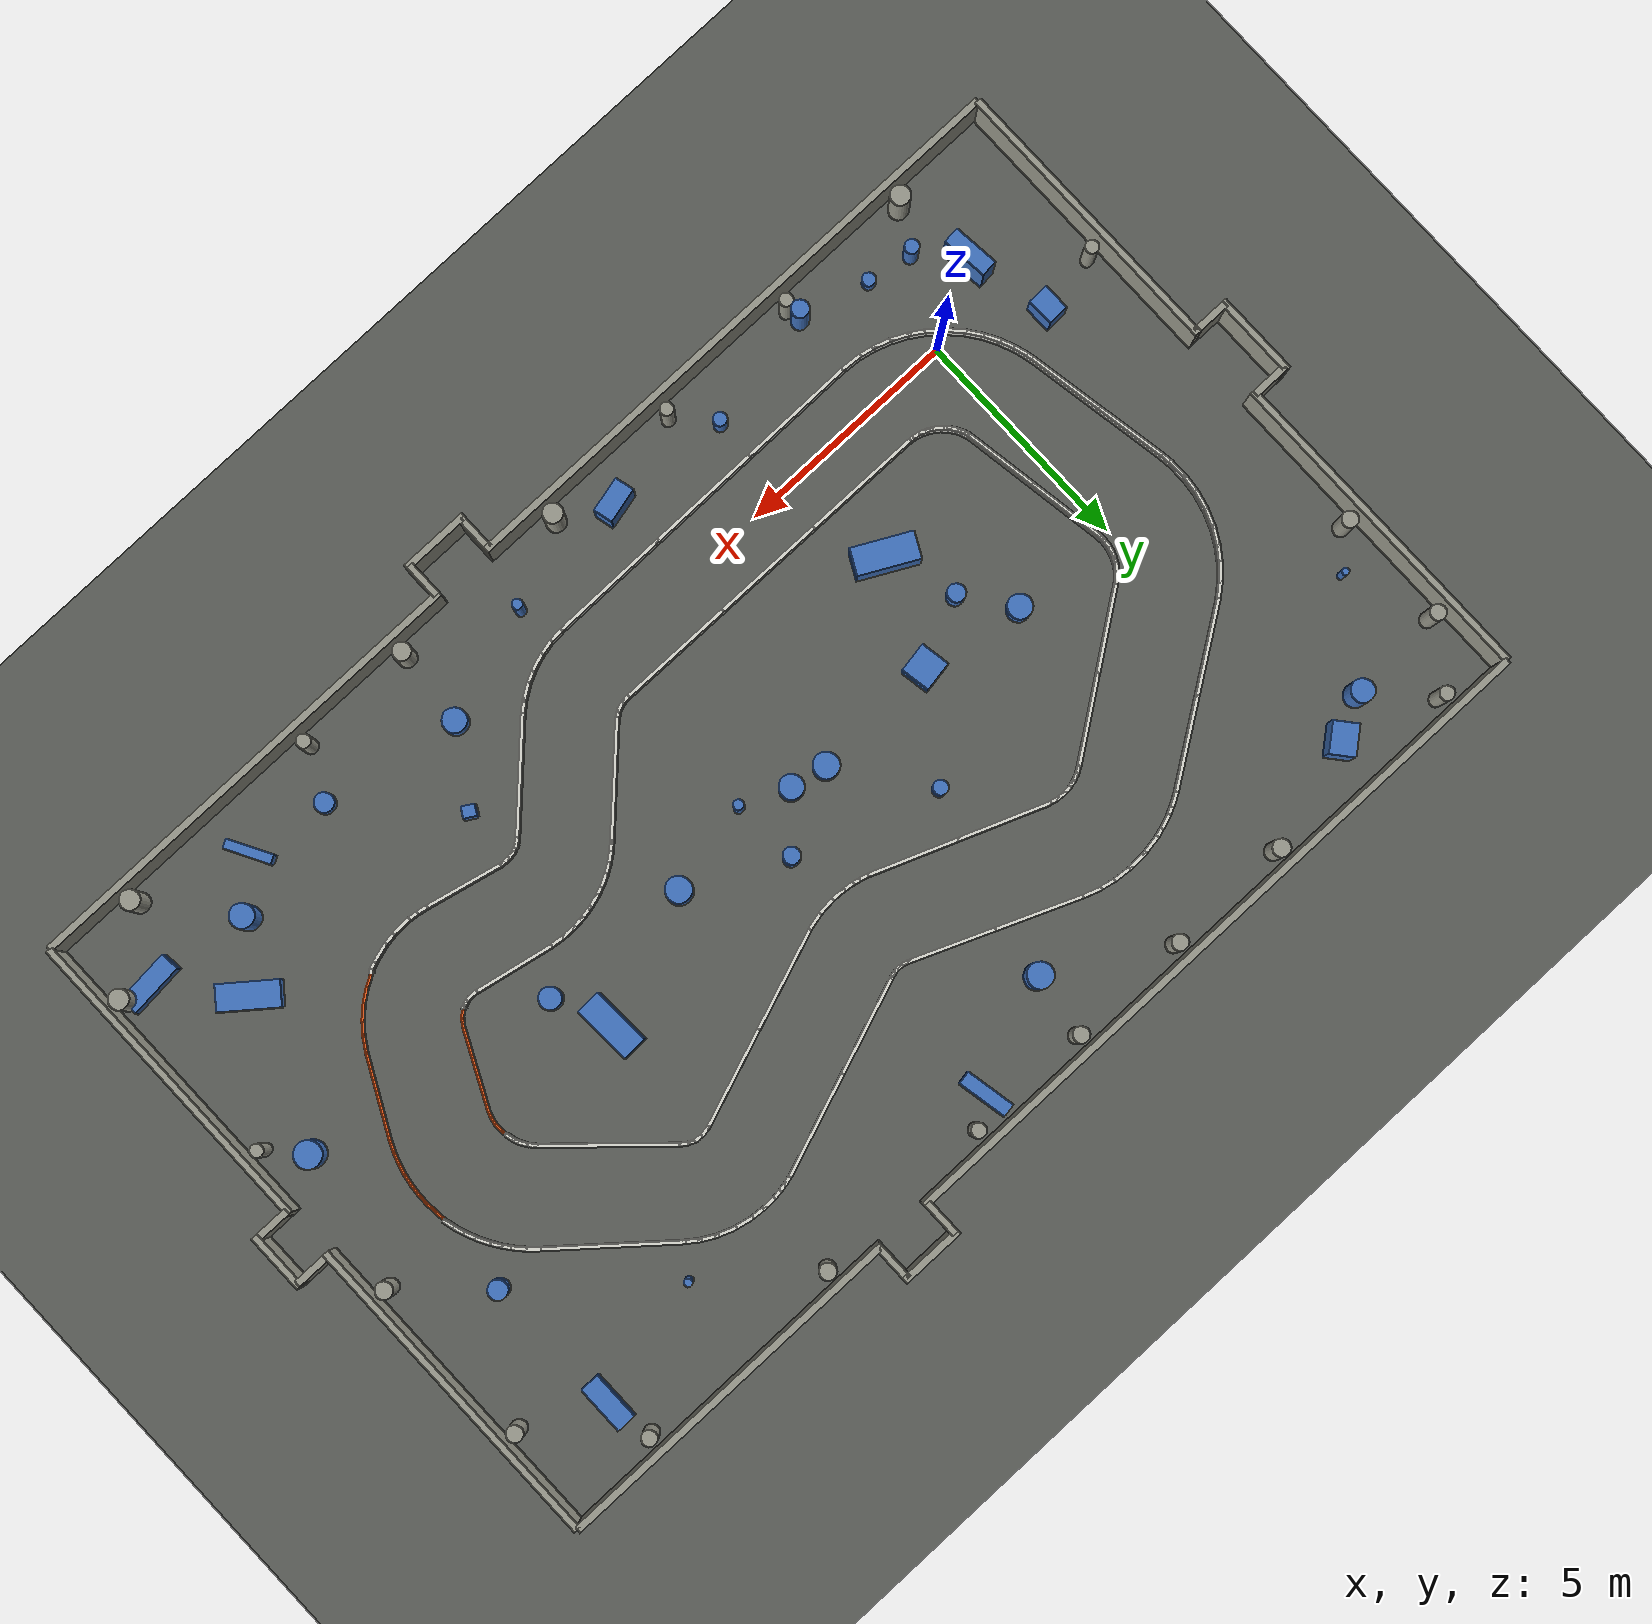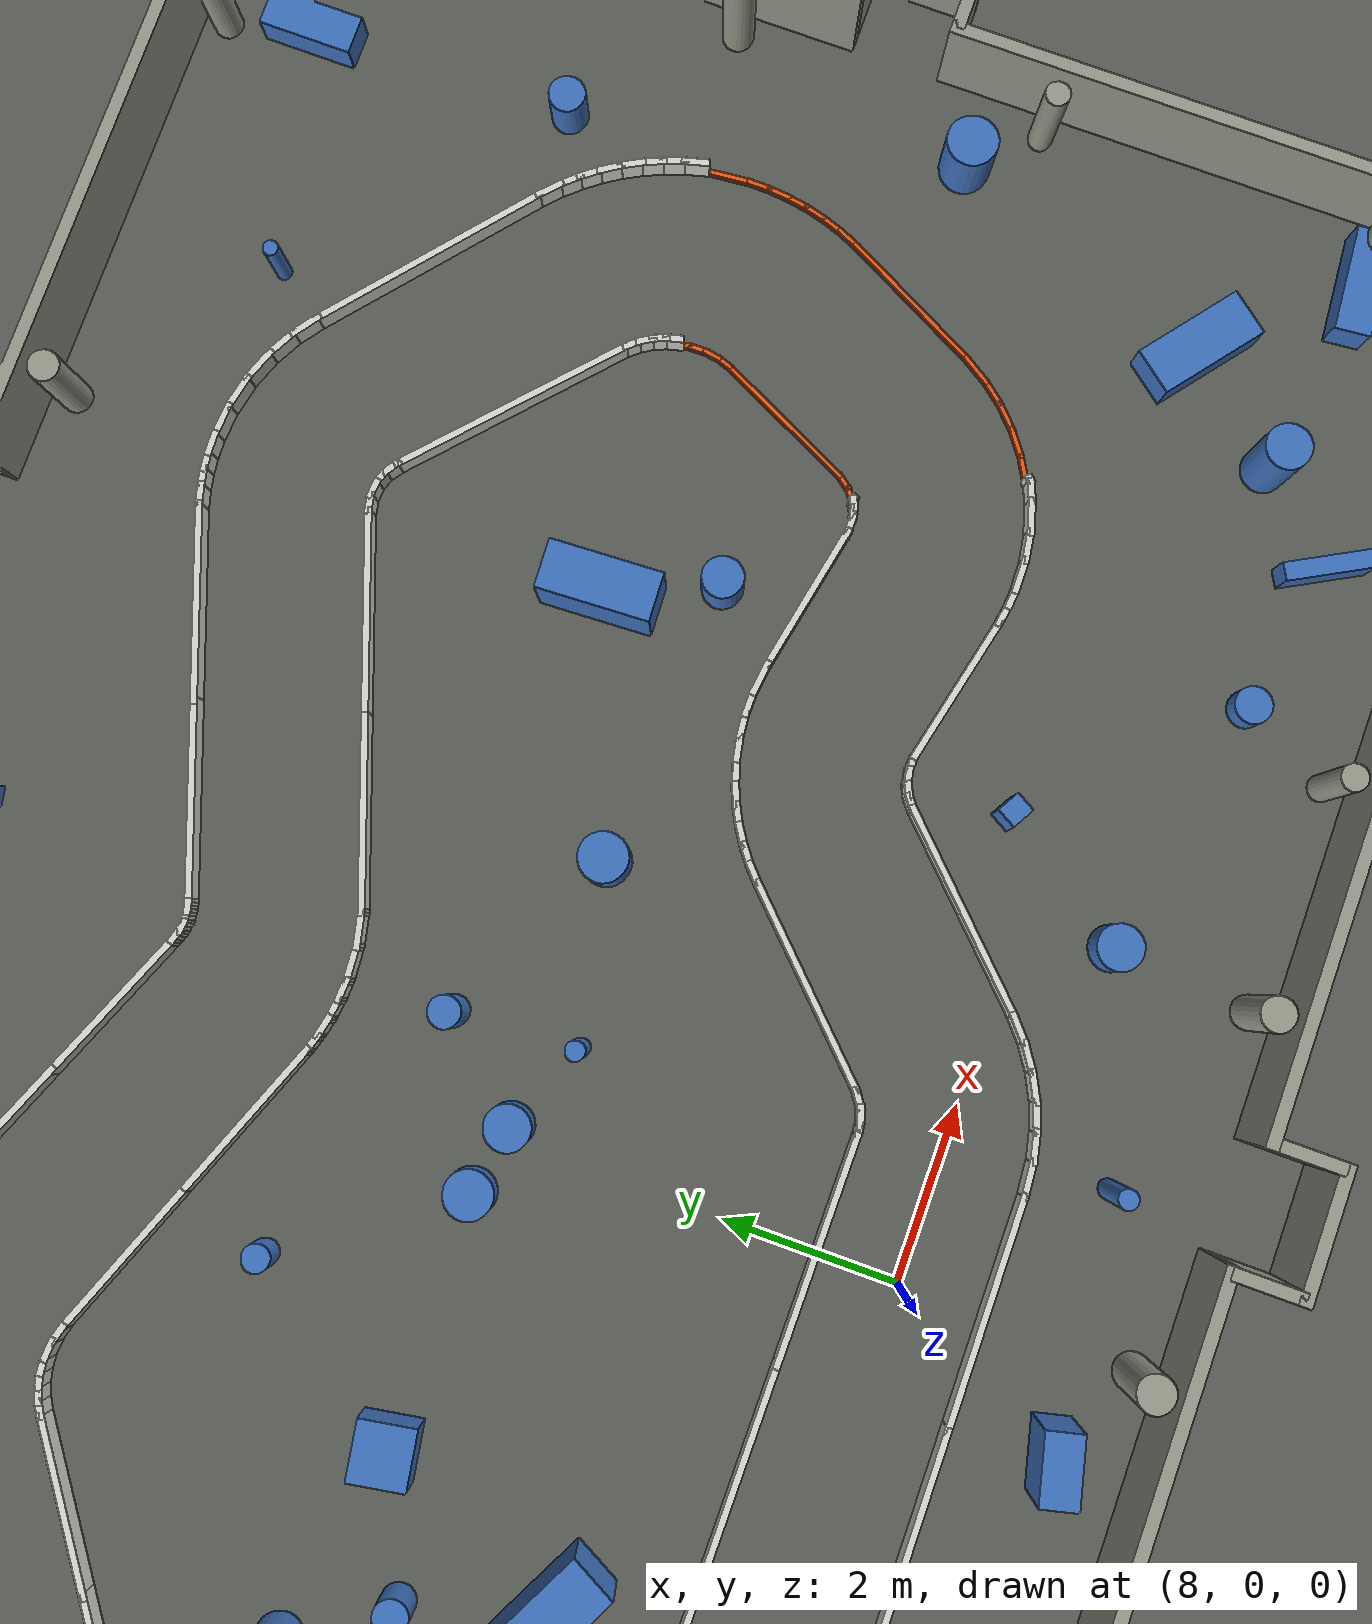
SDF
<?xml version="1.0" ?>
<sdf version="1.9">
  <!-- Generated by simulation/tools/generate_pose_dataset.py --install-gazebo-worlds from tools/pose_dataset/config/tracks.yaml (zs_roundabout_city). Do not edit by hand: change the YAML and regenerate. -->
  <world name="default">
    <physics name="default_physics" type="dart">
      <max_step_size>0.001</max_step_size>
      <real_time_factor>1.0</real_time_factor>
      <real_time_update_rate>1000.0</real_time_update_rate>
    </physics>
    <plugin filename="gz-sim-physics-system" name="gz::sim::systems::Physics" />
    <plugin filename="gz-sim-user-commands-system" name="gz::sim::systems::UserCommands" />
    <plugin filename="gz-sim-scene-broadcaster-system" name="gz::sim::systems::SceneBroadcaster" />
    <plugin filename="gz-sim-imu-system" name="gz::sim::systems::Imu" />
    <plugin filename="gz-sim-sensors-system" name="gz::sim::systems::Sensors">
      <render_engine>ogre2</render_engine>
    </plugin>
    <light type="directional" name="sun">
      <pose>0 0 10 0 0 0</pose>
      <diffuse>0.8 0.8 0.8 1</diffuse>
      <direction>-0.5 0.5 -1</direction>
      <cast_shadows>true</cast_shadows>
    </light>
    <model name="track_curb">
      <static>true</static>
      <pose>0 0 0 0 0 0</pose>
      <link name="curb_link">
        <collision name="left0_0_0_collision">
          <pose>15.970146 3.323081 0.035000 0.000000 0.000000 0.634511</pose>
          <geometry>
            <box>
              <size>0.236195 0.060000 0.070000</size>
            </box>
          </geometry>
        </collision>
        <visual name="left0_0_0_visual">
          <pose>15.970146 3.323081 0.035000 0.000000 0.000000 0.634511</pose>
          <geometry>
            <box>
              <size>0.236195 0.060000 0.070000</size>
            </box>
          </geometry>
          <material>
            <ambient>0.9 0.35 0.1 1</ambient>
            <diffuse>0.9 0.35 0.1 1</diffuse>
          </material>
        </visual>
        <collision name="left0_1_0_collision">
          <pose>16.093894 3.444819 0.035000 0.000000 0.000000 0.921238</pose>
          <geometry>
            <box>
              <size>0.234584 0.060000 0.070000</size>
            </box>
          </geometry>
        </collision>
        <visual name="left0_1_0_visual">
          <pose>16.093894 3.444819 0.035000 0.000000 0.000000 0.921238</pose>
          <geometry>
            <box>
              <size>0.234584 0.060000 0.070000</size>
            </box>
          </geometry>
          <material>
            <ambient>0.9 0.35 0.1 1</ambient>
            <diffuse>0.9 0.35 0.1 1</diffuse>
          </material>
        </visual>
        <collision name="left0_2_0_collision">
          <pose>16.530513 4.306263 0.035000 0.000000 0.000000 1.119490</pose>
          <geometry>
            <box>
              <size>1.820081 0.060000 0.070000</size>
            </box>
          </geometry>
        </collision>
        <visual name="left0_2_0_visual">
          <pose>16.530513 4.306263 0.035000 0.000000 0.000000 1.119490</pose>
          <geometry>
            <box>
              <size>1.820081 0.060000 0.070000</size>
            </box>
          </geometry>
          <material>
            <ambient>0.9 0.35 0.1 1</ambient>
            <diffuse>0.9 0.35 0.1 1</diffuse>
          </material>
        </visual>
        <collision name="left0_3_0_collision">
          <pose>16.939653 5.172351 0.035000 0.000000 0.000000 1.241788</pose>
          <geometry>
            <box>
              <size>0.216722 0.060000 0.070000</size>
            </box>
          </geometry>
        </collision>
        <visual name="left0_3_0_visual">
          <pose>16.939653 5.172351 0.035000 0.000000 0.000000 1.241788</pose>
          <geometry>
            <box>
              <size>0.216722 0.060000 0.070000</size>
            </box>
          </geometry>
          <material>
            <ambient>0.9 0.35 0.1 1</ambient>
            <diffuse>0.9 0.35 0.1 1</diffuse>
          </material>
        </visual>
        <collision name="left0_4_0_collision">
          <pose>16.978545 5.328295 0.035000 0.000000 0.000000 1.406337</pose>
          <geometry>
            <box>
              <size>0.225809 0.060000 0.070000</size>
            </box>
          </geometry>
        </collision>
        <visual name="left0_4_0_visual">
          <pose>16.978545 5.328295 0.035000 0.000000 0.000000 1.406337</pose>
          <geometry>
            <box>
              <size>0.225809 0.060000 0.070000</size>
            </box>
          </geometry>
          <material>
            <ambient>0.9 0.35 0.1 1</ambient>
            <diffuse>0.9 0.35 0.1 1</diffuse>
          </material>
        </visual>
        <collision name="left0_5_0_collision">
          <pose>16.990731 5.502282 0.035000 0.000000 0.000000 1.585837</pose>
          <geometry>
            <box>
              <size>0.244424 0.060000 0.070000</size>
            </box>
          </geometry>
        </collision>
        <visual name="left0_5_0_visual">
          <pose>16.990731 5.502282 0.035000 0.000000 0.000000 1.585837</pose>
          <geometry>
            <box>
              <size>0.244424 0.060000 0.070000</size>
            </box>
          </geometry>
          <material>
            <ambient>0.9 0.35 0.1 1</ambient>
            <diffuse>0.9 0.35 0.1 1</diffuse>
          </material>
        </visual>
        <collision name="left0_6_0_collision">
          <pose>16.980616 5.647001 0.035000 0.000000 0.000000 1.735485</pose>
          <geometry>
            <box>
              <size>0.166475 0.060000 0.070000</size>
            </box>
          </geometry>
        </collision>
        <visual name="left0_6_0_visual">
          <pose>16.980616 5.647001 0.035000 0.000000 0.000000 1.735485</pose>
          <geometry>
            <box>
              <size>0.166475 0.060000 0.070000</size>
            </box>
          </geometry>
          <material>
            <ambient>0.9 0.35 0.1 1</ambient>
            <diffuse>0.9 0.35 0.1 1</diffuse>
          </material>
        </visual>
        <collision name="left0_7_0_collision">
          <pose>16.966231 5.703283 0.035000 0.000000 0.000000 2.554404</pose>
          <geometry>
            <box>
              <size>0.073592 0.060000 0.070000</size>
            </box>
          </geometry>
        </collision>
        <visual name="left0_7_0_visual">
          <pose>16.966231 5.703283 0.035000 0.000000 0.000000 2.554404</pose>
          <geometry>
            <box>
              <size>0.073592 0.060000 0.070000</size>
            </box>
          </geometry>
          <material>
            <ambient>0.9 0.35 0.1 1</ambient>
            <diffuse>0.9 0.35 0.1 1</diffuse>
          </material>
        </visual>
        <collision name="right0_0_0_collision">
          <pose>16.908648 1.592783 0.035000 0.000000 0.000000 0.514198</pose>
          <geometry>
            <box>
              <size>0.381289 0.060000 0.070000</size>
            </box>
          </geometry>
        </collision>
        <visual name="right0_0_0_visual">
          <pose>16.908648 1.592783 0.035000 0.000000 0.000000 0.514198</pose>
          <geometry>
            <box>
              <size>0.381289 0.060000 0.070000</size>
            </box>
          </geometry>
          <material>
            <ambient>0.9 0.35 0.1 1</ambient>
            <diffuse>0.9 0.35 0.1 1</diffuse>
          </material>
        </visual>
        <collision name="right0_1_0_collision">
          <pose>17.177615 1.767659 0.035000 0.000000 0.000000 0.638742</pose>
          <geometry>
            <box>
              <size>0.381595 0.060000 0.070000</size>
            </box>
          </geometry>
        </collision>
        <visual name="right0_1_0_visual">
          <pose>17.177615 1.767659 0.035000 0.000000 0.000000 0.638742</pose>
          <geometry>
            <box>
              <size>0.381595 0.060000 0.070000</size>
            </box>
          </geometry>
          <material>
            <ambient>0.9 0.35 0.1 1</ambient>
            <diffuse>0.9 0.35 0.1 1</diffuse>
          </material>
        </visual>
        <collision name="right0_2_0_collision">
          <pose>17.423008 1.974789 0.035000 0.000000 0.000000 0.763286</pose>
          <geometry>
            <box>
              <size>0.381901 0.060000 0.070000</size>
            </box>
          </geometry>
        </collision>
        <visual name="right0_2_0_visual">
          <pose>17.423008 1.974789 0.035000 0.000000 0.000000 0.763286</pose>
          <geometry>
            <box>
              <size>0.381901 0.060000 0.070000</size>
            </box>
          </geometry>
          <material>
            <ambient>0.9 0.35 0.1 1</ambient>
            <diffuse>0.9 0.35 0.1 1</diffuse>
          </material>
        </visual>
        <collision name="right0_3_0_collision">
          <pose>17.631516 2.197962 0.035000 0.000000 0.000000 0.881600</pose>
          <geometry>
            <box>
              <size>0.350007 0.060000 0.070000</size>
            </box>
          </geometry>
        </collision>
        <visual name="right0_3_0_visual">
          <pose>17.631516 2.197962 0.035000 0.000000 0.000000 0.881600</pose>
          <geometry>
            <box>
              <size>0.350007 0.060000 0.070000</size>
            </box>
          </geometry>
          <material>
            <ambient>0.9 0.35 0.1 1</ambient>
            <diffuse>0.9 0.35 0.1 1</diffuse>
          </material>
        </visual>
        <collision name="right0_4_0_collision">
          <pose>17.818630 2.459690 0.035000 0.000000 0.000000 1.006148</pose>
          <geometry>
            <box>
              <size>0.414698 0.060000 0.070000</size>
            </box>
          </geometry>
        </collision>
        <visual name="right0_4_0_visual">
          <pose>17.818630 2.459690 0.035000 0.000000 0.000000 1.006148</pose>
          <geometry>
            <box>
              <size>0.414698 0.060000 0.070000</size>
            </box>
          </geometry>
          <material>
            <ambient>0.9 0.35 0.1 1</ambient>
            <diffuse>0.9 0.35 0.1 1</diffuse>
          </material>
        </visual>
        <collision name="right0_5_0_collision">
          <pose>18.328015 3.413927 0.035000 0.000000 0.000000 1.095017</pose>
          <geometry>
            <box>
              <size>1.869843 0.060000 0.070000</size>
            </box>
          </geometry>
        </collision>
        <visual name="right0_5_0_visual">
          <pose>18.328015 3.413927 0.035000 0.000000 0.000000 1.095017</pose>
          <geometry>
            <box>
              <size>1.869843 0.060000 0.070000</size>
            </box>
          </geometry>
          <material>
            <ambient>0.9 0.35 0.1 1</ambient>
            <diffuse>0.9 0.35 0.1 1</diffuse>
          </material>
        </visual>
        <collision name="right0_6_0_collision">
          <pose>18.790626 4.328469 0.035000 0.000000 0.000000 1.158779</pose>
          <geometry>
            <box>
              <size>0.300364 0.060000 0.070000</size>
            </box>
          </geometry>
        </collision>
        <visual name="right0_6_0_visual">
          <pose>18.790626 4.328469 0.035000 0.000000 0.000000 1.158779</pose>
          <geometry>
            <box>
              <size>0.300364 0.060000 0.070000</size>
            </box>
          </geometry>
          <material>
            <ambient>0.9 0.35 0.1 1</ambient>
            <diffuse>0.9 0.35 0.1 1</diffuse>
          </material>
        </visual>
        <collision name="right0_7_0_collision">
          <pose>18.877982 4.552275 0.035000 0.000000 0.000000 1.238518</pose>
          <geometry>
            <box>
              <size>0.300520 0.060000 0.070000</size>
            </box>
          </geometry>
        </collision>
        <visual name="right0_7_0_visual">
          <pose>18.877982 4.552275 0.035000 0.000000 0.000000 1.238518</pose>
          <geometry>
            <box>
              <size>0.300520 0.060000 0.070000</size>
            </box>
          </geometry>
          <material>
            <ambient>0.9 0.35 0.1 1</ambient>
            <diffuse>0.9 0.35 0.1 1</diffuse>
          </material>
        </visual>
        <collision name="right0_8_0_collision">
          <pose>18.947279 4.782479 0.035000 0.000000 0.000000 1.318258</pose>
          <geometry>
            <box>
              <size>0.300677 0.060000 0.070000</size>
            </box>
          </geometry>
        </collision>
        <visual name="right0_8_0_visual">
          <pose>18.947279 4.782479 0.035000 0.000000 0.000000 1.318258</pose>
          <geometry>
            <box>
              <size>0.300677 0.060000 0.070000</size>
            </box>
          </geometry>
          <material>
            <ambient>0.9 0.35 0.1 1</ambient>
            <diffuse>0.9 0.35 0.1 1</diffuse>
          </material>
        </visual>
        <collision name="right0_9_0_collision">
          <pose>18.998051 5.017624 0.035000 0.000000 0.000000 1.397997</pose>
          <geometry>
            <box>
              <size>0.300834 0.060000 0.070000</size>
            </box>
          </geometry>
        </collision>
        <visual name="right0_9_0_visual">
          <pose>18.998051 5.017624 0.035000 0.000000 0.000000 1.397997</pose>
          <geometry>
            <box>
              <size>0.300834 0.060000 0.070000</size>
            </box>
          </geometry>
          <material>
            <ambient>0.9 0.35 0.1 1</ambient>
            <diffuse>0.9 0.35 0.1 1</diffuse>
          </material>
        </visual>
        <collision name="right0_10_0_collision">
          <pose>19.029953 5.256221 0.035000 0.000000 0.000000 1.477737</pose>
          <geometry>
            <box>
              <size>0.300990 0.060000 0.070000</size>
            </box>
          </geometry>
        </collision>
        <visual name="right0_10_0_visual">
          <pose>19.029953 5.256221 0.035000 0.000000 0.000000 1.477737</pose>
          <geometry>
            <box>
              <size>0.300990 0.060000 0.070000</size>
            </box>
          </geometry>
          <material>
            <ambient>0.9 0.35 0.1 1</ambient>
            <diffuse>0.9 0.35 0.1 1</diffuse>
          </material>
        </visual>
        <collision name="right0_11_0_collision">
          <pose>19.042756 5.496757 0.035000 0.000000 0.000000 1.557476</pose>
          <geometry>
            <box>
              <size>0.301147 0.060000 0.070000</size>
            </box>
          </geometry>
        </collision>
        <visual name="right0_11_0_visual">
          <pose>19.042756 5.496757 0.035000 0.000000 0.000000 1.557476</pose>
          <geometry>
            <box>
              <size>0.301147 0.060000 0.070000</size>
            </box>
          </geometry>
          <material>
            <ambient>0.9 0.35 0.1 1</ambient>
            <diffuse>0.9 0.35 0.1 1</diffuse>
          </material>
        </visual>
        <collision name="right0_12_0_collision">
          <pose>19.020485 5.872923 0.035000 0.000000 0.000000 1.663938</pose>
          <geometry>
            <box>
              <size>0.573431 0.060000 0.070000</size>
            </box>
          </geometry>
        </collision>
        <visual name="right0_12_0_visual">
          <pose>19.020485 5.872923 0.035000 0.000000 0.000000 1.663938</pose>
          <geometry>
            <box>
              <size>0.573431 0.060000 0.070000</size>
            </box>
          </geometry>
          <material>
            <ambient>0.9 0.35 0.1 1</ambient>
            <diffuse>0.9 0.35 0.1 1</diffuse>
          </material>
        </visual>
      </link>
    </model>
    <model name="track_feature">
      <static>true</static>
      <pose>0 0 0 0 0 0</pose>
      <link name="feature_link">
        <collision name="feat_box_2_collision">
          <pose>6.893507 -2.075079 0.432119 0.000000 0.000000 0.234095</pose>
          <geometry>
            <box>
              <size>0.784161 0.426067 0.864237</size>
            </box>
          </geometry>
        </collision>
        <visual name="feat_box_2_visual">
          <pose>6.893507 -2.075079 0.432119 0.000000 0.000000 0.234095</pose>
          <geometry>
            <box>
              <size>0.784161 0.426067 0.864237</size>
            </box>
          </geometry>
          <material>
            <ambient>0.25 0.45 0.75 1</ambient>
            <diffuse>0.25 0.45 0.75 1</diffuse>
          </material>
        </visual>
        <collision name="feat_box_4_collision">
          <pose>16.920263 -1.889733 0.225783 0.000000 0.000000 2.068316</pose>
          <geometry>
            <box>
              <size>1.015036 0.210191 0.451566</size>
            </box>
          </geometry>
        </collision>
        <visual name="feat_box_4_visual">
          <pose>16.920263 -1.889733 0.225783 0.000000 0.000000 2.068316</pose>
          <geometry>
            <box>
              <size>1.015036 0.210191 0.451566</size>
            </box>
          </geometry>
          <material>
            <ambient>0.25 0.45 0.75 1</ambient>
            <diffuse>0.25 0.45 0.75 1</diffuse>
          </material>
        </visual>
        <collision name="feat_box_7_collision">
          <pose>19.027106 10.913917 0.205095 0.000000 0.000000 -1.572901</pose>
          <geometry>
            <box>
              <size>1.084053 0.437793 0.410189</size>
            </box>
          </geometry>
        </collision>
        <visual name="feat_box_7_visual">
          <pose>19.027106 10.913917 0.205095 0.000000 0.000000 -1.572901</pose>
          <geometry>
            <box>
              <size>1.084053 0.437793 0.410189</size>
            </box>
          </geometry>
          <material>
            <ambient>0.25 0.45 0.75 1</ambient>
            <diffuse>0.25 0.45 0.75 1</diffuse>
          </material>
        </visual>
        <collision name="feat_box_8_collision">
          <pose>13.180462 0.500408 0.288573 0.000000 0.000000 1.049483</pose>
          <geometry>
            <box>
              <size>0.250118 0.284658 0.577145</size>
            </box>
          </geometry>
        </collision>
        <visual name="feat_box_8_visual">
          <pose>13.180462 0.500408 0.288573 0.000000 0.000000 1.049483</pose>
          <geometry>
            <box>
              <size>0.250118 0.284658 0.577145</size>
            </box>
          </geometry>
          <material>
            <ambient>0.25 0.45 0.75 1</ambient>
            <diffuse>0.25 0.45 0.75 1</diffuse>
          </material>
        </visual>
        <collision name="feat_box_10_collision">
          <pose>4.596318 4.539169 0.260648 0.000000 0.000000 -1.405028</pose>
          <geometry>
            <box>
              <size>0.649376 0.665287 0.521296</size>
            </box>
          </geometry>
        </collision>
        <visual name="feat_box_10_visual">
          <pose>4.596318 4.539169 0.260648 0.000000 0.000000 -1.405028</pose>
          <geometry>
            <box>
              <size>0.649376 0.665287 0.521296</size>
            </box>
          </geometry>
          <material>
            <ambient>0.25 0.45 0.75 1</ambient>
            <diffuse>0.25 0.45 0.75 1</diffuse>
          </material>
        </visual>
        <collision name="feat_box_15_collision">
          <pose>9.478529 11.540616 0.271835 0.000000 0.000000 1.760429</pose>
          <geometry>
            <box>
              <size>1.097475 0.296877 0.543671</size>
            </box>
          </geometry>
        </collision>
        <visual name="feat_box_15_visual">
          <pose>9.478529 11.540616 0.271835 0.000000 0.000000 1.760429</pose>
          <geometry>
            <box>
              <size>1.097475 0.296877 0.543671</size>
            </box>
          </geometry>
          <material>
            <ambient>0.25 0.45 0.75 1</ambient>
            <diffuse>0.25 0.45 0.75 1</diffuse>
          </material>
        </visual>
        <collision name="feat_box_16_collision">
          <pose>20.118092 -1.274449 0.233364 0.000000 0.000000 0.086087</pose>
          <geometry>
            <box>
              <size>1.220117 0.411430 0.466729</size>
            </box>
          </geometry>
        </collision>
        <visual name="feat_box_16_visual">
          <pose>20.118092 -1.274449 0.233364 0.000000 0.000000 0.086087</pose>
          <geometry>
            <box>
              <size>1.220117 0.411430 0.466729</size>
            </box>
          </geometry>
          <material>
            <ambient>0.25 0.45 0.75 1</ambient>
            <diffuse>0.25 0.45 0.75 1</diffuse>
          </material>
        </visual>
        <collision name="feat_box_17_collision">
          <pose>18.837482 0.220410 0.234092 0.000000 0.000000 -0.667305</pose>
          <geometry>
            <box>
              <size>1.301226 0.559441 0.468183</size>
            </box>
          </geometry>
        </collision>
        <visual name="feat_box_17_visual">
          <pose>18.837482 0.220410 0.234092 0.000000 0.000000 -0.667305</pose>
          <geometry>
            <box>
              <size>1.301226 0.559441 0.468183</size>
            </box>
          </geometry>
          <material>
            <ambient>0.25 0.45 0.75 1</ambient>
            <diffuse>0.25 0.45 0.75 1</diffuse>
          </material>
        </visual>
        <collision name="feat_box_22_collision">
          <pose>13.970763 5.545568 0.465767 0.000000 0.000000 -1.526188</pose>
          <geometry>
            <box>
              <size>1.295734 0.558887 0.931534</size>
            </box>
          </geometry>
        </collision>
        <visual name="feat_box_22_visual">
          <pose>13.970763 5.545568 0.465767 0.000000 0.000000 -1.526188</pose>
          <geometry>
            <box>
              <size>1.295734 0.558887 0.931534</size>
            </box>
          </geometry>
          <material>
            <ambient>0.25 0.45 0.75 1</ambient>
            <diffuse>0.25 0.45 0.75 1</diffuse>
          </material>
        </visual>
        <collision name="feat_box_23_collision">
          <pose>3.658291 2.359002 0.386819 0.000000 0.000000 2.662780</pose>
          <geometry>
            <box>
              <size>1.337380 0.588841 0.773637</size>
            </box>
          </geometry>
        </collision>
        <visual name="feat_box_23_visual">
          <pose>3.658291 2.359002 0.386819 0.000000 0.000000 2.662780</pose>
          <geometry>
            <box>
              <size>1.337380 0.588841 0.773637</size>
            </box>
          </geometry>
          <material>
            <ambient>0.25 0.45 0.75 1</ambient>
            <diffuse>0.25 0.45 0.75 1</diffuse>
          </material>
        </visual>
        <collision name="feat_box_27_collision">
          <pose>-1.650008 -0.885950 0.545496 0.000000 0.000000 1.668477</pose>
          <geometry>
            <box>
              <size>1.020176 0.366927 1.090992</size>
            </box>
          </geometry>
        </collision>
        <visual name="feat_box_27_visual">
          <pose>-1.650008 -0.885950 0.545496 0.000000 0.000000 1.668477</pose>
          <geometry>
            <box>
              <size>1.020176 0.366927 1.090992</size>
            </box>
          </geometry>
          <material>
            <ambient>0.25 0.45 0.75 1</ambient>
            <diffuse>0.25 0.45 0.75 1</diffuse>
          </material>
        </visual>
        <collision name="feat_box_30_collision">
          <pose>-2.133260 0.902215 0.367506 0.000000 0.000000 0.016267</pose>
          <geometry>
            <box>
              <size>0.464780 0.596565 0.735012</size>
            </box>
          </geometry>
        </collision>
        <visual name="feat_box_30_visual">
          <pose>-2.133260 0.902215 0.367506 0.000000 0.000000 0.016267</pose>
          <geometry>
            <box>
              <size>0.464780 0.596565 0.735012</size>
            </box>
          </geometry>
          <material>
            <ambient>0.25 0.45 0.75 1</ambient>
            <diffuse>0.25 0.45 0.75 1</diffuse>
          </material>
        </visual>
        <collision name="feat_box_35_collision">
          <pose>-0.467199 11.218057 0.410643 0.000000 0.000000 2.260509</pose>
          <geometry>
            <box>
              <size>0.548164 0.681923 0.821285</size>
            </box>
          </geometry>
        </collision>
        <visual name="feat_box_35_visual">
          <pose>-0.467199 11.218057 0.410643 0.000000 0.000000 2.260509</pose>
          <geometry>
            <box>
              <size>0.548164 0.681923 0.821285</size>
            </box>
          </geometry>
          <material>
            <ambient>0.25 0.45 0.75 1</ambient>
            <diffuse>0.25 0.45 0.75 1</diffuse>
          </material>
        </visual>
        <collision name="feat_cyl_1_collision">
          <pose>4.223443 -1.863348 0.320669 0.000000 0.000000 0.000000</pose>
          <geometry>
            <cylinder>
              <radius>0.146870</radius>
              <length>0.641337</length>
            </cylinder>
          </geometry>
        </collision>
        <visual name="feat_cyl_1_visual">
          <pose>4.223443 -1.863348 0.320669 0.000000 0.000000 0.000000</pose>
          <geometry>
            <cylinder>
              <radius>0.146870</radius>
              <length>0.641337</length>
            </cylinder>
          </geometry>
          <material>
            <ambient>0.25 0.45 0.75 1</ambient>
            <diffuse>0.25 0.45 0.75 1</diffuse>
          </material>
        </visual>
        <collision name="feat_cyl_3_collision">
          <pose>2.383929 4.931580 0.233914 0.000000 0.000000 0.000000</pose>
          <geometry>
            <cylinder>
              <radius>0.263021</radius>
              <length>0.467828</length>
            </cylinder>
          </geometry>
        </collision>
        <visual name="feat_cyl_3_visual">
          <pose>2.383929 4.931580 0.233914 0.000000 0.000000 0.000000</pose>
          <geometry>
            <cylinder>
              <radius>0.263021</radius>
              <length>0.467828</length>
            </cylinder>
          </geometry>
          <material>
            <ambient>0.25 0.45 0.75 1</ambient>
            <diffuse>0.25 0.45 0.75 1</diffuse>
          </material>
        </visual>
        <collision name="feat_cyl_5_collision">
          <pose>19.104657 7.824802 0.302177 0.000000 0.000000 0.000000</pose>
          <geometry>
            <cylinder>
              <radius>0.210776</radius>
              <length>0.604354</length>
            </cylinder>
          </geometry>
        </collision>
        <visual name="feat_cyl_5_visual">
          <pose>19.104657 7.824802 0.302177 0.000000 0.000000 0.000000</pose>
          <geometry>
            <cylinder>
              <radius>0.210776</radius>
              <length>0.604354</length>
            </cylinder>
          </geometry>
          <material>
            <ambient>0.25 0.45 0.75 1</ambient>
            <diffuse>0.25 0.45 0.75 1</diffuse>
          </material>
        </visual>
        <collision name="feat_cyl_6_collision">
          <pose>9.107483 5.501725 0.417309 0.000000 0.000000 0.000000</pose>
          <geometry>
            <cylinder>
              <radius>0.183211</radius>
              <length>0.834617</length>
            </cylinder>
          </geometry>
        </collision>
        <visual name="feat_cyl_6_visual">
          <pose>9.107483 5.501725 0.417309 0.000000 0.000000 0.000000</pose>
          <geometry>
            <cylinder>
              <radius>0.183211</radius>
              <length>0.834617</length>
            </cylinder>
          </geometry>
          <material>
            <ambient>0.25 0.45 0.75 1</ambient>
            <diffuse>0.25 0.45 0.75 1</diffuse>
          </material>
        </visual>
        <collision name="feat_cyl_9_collision">
          <pose>20.036438 3.360670 0.398969 0.000000 0.000000 0.000000</pose>
          <geometry>
            <cylinder>
              <radius>0.293115</radius>
              <length>0.797938</length>
            </cylinder>
          </geometry>
        </collision>
        <visual name="feat_cyl_9_visual">
          <pose>20.036438 3.360670 0.398969 0.000000 0.000000 0.000000</pose>
          <geometry>
            <cylinder>
              <radius>0.293115</radius>
              <length>0.797938</length>
            </cylinder>
          </geometry>
          <material>
            <ambient>0.25 0.45 0.75 1</ambient>
            <diffuse>0.25 0.45 0.75 1</diffuse>
          </material>
        </visual>
        <collision name="feat_cyl_11_collision">
          <pose>-2.811884 8.826324 0.314941 0.000000 0.000000 0.000000</pose>
          <geometry>
            <cylinder>
              <radius>0.075633</radius>
              <length>0.629882</length>
            </cylinder>
          </geometry>
        </collision>
        <visual name="feat_cyl_11_visual">
          <pose>-2.811884 8.826324 0.314941 0.000000 0.000000 0.000000</pose>
          <geometry>
            <cylinder>
              <radius>0.075633</radius>
              <length>0.629882</length>
            </cylinder>
          </geometry>
          <material>
            <ambient>0.25 0.45 0.75 1</ambient>
            <diffuse>0.25 0.45 0.75 1</diffuse>
          </material>
        </visual>
        <collision name="feat_cyl_12_collision">
          <pose>-0.909044 -1.782525 0.448977 0.000000 0.000000 0.000000</pose>
          <geometry>
            <cylinder>
              <radius>0.154599</radius>
              <length>0.897953</length>
            </cylinder>
          </geometry>
        </collision>
        <visual name="feat_cyl_12_visual">
          <pose>-0.909044 -1.782525 0.448977 0.000000 0.000000 0.000000</pose>
          <geometry>
            <cylinder>
              <radius>0.154599</radius>
              <length>0.897953</length>
            </cylinder>
          </geometry>
          <material>
            <ambient>0.25 0.45 0.75 1</ambient>
            <diffuse>0.25 0.45 0.75 1</diffuse>
          </material>
        </visual>
        <collision name="feat_cyl_13_collision">
          <pose>14.498074 4.321462 0.327709 0.000000 0.000000 0.000000</pose>
          <geometry>
            <cylinder>
              <radius>0.237108</radius>
              <length>0.655418</length>
            </cylinder>
          </geometry>
        </collision>
        <visual name="feat_cyl_13_visual">
          <pose>14.498074 4.321462 0.327709 0.000000 0.000000 0.000000</pose>
          <geometry>
            <cylinder>
              <radius>0.237108</radius>
              <length>0.655418</length>
            </cylinder>
          </geometry>
          <material>
            <ambient>0.25 0.45 0.75 1</ambient>
            <diffuse>0.25 0.45 0.75 1</diffuse>
          </material>
        </visual>
        <collision name="feat_cyl_14_collision">
          <pose>6.010424 6.502096 0.240069 0.000000 0.000000 0.000000</pose>
          <geometry>
            <cylinder>
              <radius>0.158849</radius>
              <length>0.480137</length>
            </cylinder>
          </geometry>
        </collision>
        <visual name="feat_cyl_14_visual">
          <pose>6.010424 6.502096 0.240069 0.000000 0.000000 0.000000</pose>
          <geometry>
            <cylinder>
              <radius>0.158849</radius>
              <length>0.480137</length>
            </cylinder>
          </geometry>
          <material>
            <ambient>0.25 0.45 0.75 1</ambient>
            <diffuse>0.25 0.45 0.75 1</diffuse>
          </material>
        </visual>
        <collision name="feat_cyl_18_collision">
          <pose>3.140112 3.880807 0.289773 0.000000 0.000000 0.000000</pose>
          <geometry>
            <cylinder>
              <radius>0.194393</radius>
              <length>0.579545</length>
            </cylinder>
          </geometry>
        </collision>
        <visual name="feat_cyl_18_visual">
          <pose>3.140112 3.880807 0.289773 0.000000 0.000000 0.000000</pose>
          <geometry>
            <cylinder>
              <radius>0.194393</radius>
              <length>0.579545</length>
            </cylinder>
          </geometry>
          <material>
            <ambient>0.25 0.45 0.75 1</ambient>
            <diffuse>0.25 0.45 0.75 1</diffuse>
          </material>
        </visual>
        <collision name="feat_cyl_19_collision">
          <pose>11.194217 4.484155 0.447290 0.000000 0.000000 0.000000</pose>
          <geometry>
            <cylinder>
              <radius>0.278460</radius>
              <length>0.894581</length>
            </cylinder>
          </geometry>
        </collision>
        <visual name="feat_cyl_19_visual">
          <pose>11.194217 4.484155 0.447290 0.000000 0.000000 0.000000</pose>
          <geometry>
            <cylinder>
              <radius>0.278460</radius>
              <length>0.894581</length>
            </cylinder>
          </geometry>
          <material>
            <ambient>0.25 0.45 0.75 1</ambient>
            <diffuse>0.25 0.45 0.75 1</diffuse>
          </material>
        </visual>
        <collision name="feat_cyl_20_collision">
          <pose>9.709332 -1.808585 0.540024 0.000000 0.000000 0.000000</pose>
          <geometry>
            <cylinder>
              <radius>0.112691</radius>
              <length>1.080048</length>
            </cylinder>
          </geometry>
        </collision>
        <visual name="feat_cyl_20_visual">
          <pose>9.709332 -1.808585 0.540024 0.000000 0.000000 0.000000</pose>
          <geometry>
            <cylinder>
              <radius>0.112691</radius>
              <length>1.080048</length>
            </cylinder>
          </geometry>
          <material>
            <ambient>0.25 0.45 0.75 1</ambient>
            <diffuse>0.25 0.45 0.75 1</diffuse>
          </material>
        </visual>
        <collision name="feat_cyl_21_collision">
          <pose>15.174839 -1.598895 0.185346 0.000000 0.000000 0.000000</pose>
          <geometry>
            <cylinder>
              <radius>0.211595</radius>
              <length>0.370692</length>
            </cylinder>
          </geometry>
        </collision>
        <visual name="feat_cyl_21_visual">
          <pose>15.174839 -1.598895 0.185346 0.000000 0.000000 0.000000</pose>
          <geometry>
            <cylinder>
              <radius>0.211595</radius>
              <length>0.370692</length>
            </cylinder>
          </geometry>
          <material>
            <ambient>0.25 0.45 0.75 1</ambient>
            <diffuse>0.25 0.45 0.75 1</diffuse>
          </material>
        </visual>
        <collision name="feat_cyl_24_collision">
          <pose>7.136881 10.542836 0.511295 0.000000 0.000000 0.000000</pose>
          <geometry>
            <cylinder>
              <radius>0.277282</radius>
              <length>1.022590</length>
            </cylinder>
          </geometry>
        </collision>
        <visual name="feat_cyl_24_visual">
          <pose>7.136881 10.542836 0.511295 0.000000 0.000000 0.000000</pose>
          <geometry>
            <cylinder>
              <radius>0.277282</radius>
              <length>1.022590</length>
            </cylinder>
          </geometry>
          <material>
            <ambient>0.25 0.45 0.75 1</ambient>
            <diffuse>0.25 0.45 0.75 1</diffuse>
          </material>
        </visual>
        <collision name="feat_cyl_25_collision">
          <pose>0.077756 -1.961062 0.176676 0.000000 0.000000 0.000000</pose>
          <geometry>
            <cylinder>
              <radius>0.145638</radius>
              <length>0.353352</length>
            </cylinder>
          </geometry>
        </collision>
        <visual name="feat_cyl_25_visual">
          <pose>0.077756 -1.961062 0.176676 0.000000 0.000000 0.000000</pose>
          <geometry>
            <cylinder>
              <radius>0.145638</radius>
              <length>0.353352</length>
            </cylinder>
          </geometry>
          <material>
            <ambient>0.25 0.45 0.75 1</ambient>
            <diffuse>0.25 0.45 0.75 1</diffuse>
          </material>
        </visual>
        <collision name="feat_cyl_26_collision">
          <pose>8.167130 4.482782 0.245720 0.000000 0.000000 0.000000</pose>
          <geometry>
            <cylinder>
              <radius>0.261555</radius>
              <length>0.491441</length>
            </cylinder>
          </geometry>
        </collision>
        <visual name="feat_cyl_26_visual">
          <pose>8.167130 4.482782 0.245720 0.000000 0.000000 0.000000</pose>
          <geometry>
            <cylinder>
              <radius>0.261555</radius>
              <length>0.491441</length>
            </cylinder>
          </geometry>
          <material>
            <ambient>0.25 0.45 0.75 1</ambient>
            <diffuse>0.25 0.45 0.75 1</diffuse>
          </material>
        </visual>
        <collision name="feat_cyl_28_collision">
          <pose>9.198717 4.060944 0.487114 0.000000 0.000000 0.000000</pose>
          <geometry>
            <cylinder>
              <radius>0.111276</radius>
              <length>0.974229</length>
            </cylinder>
          </geometry>
        </collision>
        <visual name="feat_cyl_28_visual">
          <pose>9.198717 4.060944 0.487114 0.000000 0.000000 0.000000</pose>
          <geometry>
            <cylinder>
              <radius>0.111276</radius>
              <length>0.974229</length>
            </cylinder>
          </geometry>
          <material>
            <ambient>0.25 0.45 0.75 1</ambient>
            <diffuse>0.25 0.45 0.75 1</diffuse>
          </material>
        </visual>
        <collision name="feat_cyl_29_collision">
          <pose>-1.357089 10.770163 0.497809 0.000000 0.000000 0.000000</pose>
          <geometry>
            <cylinder>
              <radius>0.248260</radius>
              <length>0.995617</length>
            </cylinder>
          </geometry>
        </collision>
        <visual name="feat_cyl_29_visual">
          <pose>-1.357089 10.770163 0.497809 0.000000 0.000000 0.000000</pose>
          <geometry>
            <cylinder>
              <radius>0.248260</radius>
              <length>0.995617</length>
            </cylinder>
          </geometry>
          <material>
            <ambient>0.25 0.45 0.75 1</ambient>
            <diffuse>0.25 0.45 0.75 1</diffuse>
          </material>
        </visual>
        <collision name="feat_cyl_31_collision">
          <pose>17.825074 -0.949603 0.521569 0.000000 0.000000 0.000000</pose>
          <geometry>
            <cylinder>
              <radius>0.259058</radius>
              <length>1.043137</length>
            </cylinder>
          </geometry>
        </collision>
        <visual name="feat_cyl_31_visual">
          <pose>17.825074 -0.949603 0.521569 0.000000 0.000000 0.000000</pose>
          <geometry>
            <cylinder>
              <radius>0.259058</radius>
              <length>1.043137</length>
            </cylinder>
          </geometry>
          <material>
            <ambient>0.25 0.45 0.75 1</ambient>
            <diffuse>0.25 0.45 0.75 1</diffuse>
          </material>
        </visual>
        <collision name="feat_cyl_32_collision">
          <pose>1.616559 -2.333221 0.577090 0.000000 0.000000 0.000000</pose>
          <geometry>
            <cylinder>
              <radius>0.191269</radius>
              <length>1.154180</length>
            </cylinder>
          </geometry>
        </collision>
        <visual name="feat_cyl_32_visual">
          <pose>1.616559 -2.333221 0.577090 0.000000 0.000000 0.000000</pose>
          <geometry>
            <cylinder>
              <radius>0.191269</radius>
              <length>1.154180</length>
            </cylinder>
          </geometry>
          <material>
            <ambient>0.25 0.45 0.75 1</ambient>
            <diffuse>0.25 0.45 0.75 1</diffuse>
          </material>
        </visual>
        <collision name="feat_cyl_33_collision">
          <pose>12.170189 -1.028893 0.270507 0.000000 0.000000 0.000000</pose>
          <geometry>
            <cylinder>
              <radius>0.261611</radius>
              <length>0.541013</length>
            </cylinder>
          </geometry>
        </collision>
        <visual name="feat_cyl_33_visual">
          <pose>12.170189 -1.028893 0.270507 0.000000 0.000000 0.000000</pose>
          <geometry>
            <cylinder>
              <radius>0.261611</radius>
              <length>0.541013</length>
            </cylinder>
          </geometry>
          <material>
            <ambient>0.25 0.45 0.75 1</ambient>
            <diffuse>0.25 0.45 0.75 1</diffuse>
          </material>
        </visual>
        <collision name="feat_cyl_34_collision">
          <pose>7.363234 4.634075 0.195423 0.000000 0.000000 0.000000</pose>
          <geometry>
            <cylinder>
              <radius>0.278139</radius>
              <length>0.390846</length>
            </cylinder>
          </geometry>
        </collision>
        <visual name="feat_cyl_34_visual">
          <pose>7.363234 4.634075 0.195423 0.000000 0.000000 0.000000</pose>
          <geometry>
            <cylinder>
              <radius>0.278139</radius>
              <length>0.390846</length>
            </cylinder>
          </geometry>
          <material>
            <ambient>0.25 0.45 0.75 1</ambient>
            <diffuse>0.25 0.45 0.75 1</diffuse>
          </material>
        </visual>
        <collision name="feat_cyl_36_collision">
          <pose>16.262033 10.248789 0.385588 0.000000 0.000000 0.000000</pose>
          <geometry>
            <cylinder>
              <radius>0.088064</radius>
              <length>0.771176</length>
            </cylinder>
          </geometry>
        </collision>
        <visual name="feat_cyl_36_visual">
          <pose>16.262033 10.248789 0.385588 0.000000 0.000000 0.000000</pose>
          <geometry>
            <cylinder>
              <radius>0.088064</radius>
              <length>0.771176</length>
            </cylinder>
          </geometry>
          <material>
            <ambient>0.25 0.45 0.75 1</ambient>
            <diffuse>0.25 0.45 0.75 1</diffuse>
          </material>
        </visual>
      </link>
    </model>
    <model name="track_ground">
      <static>true</static>
      <pose>0 0 0 0 0 0</pose>
      <link name="ground_link">
        <collision name="ground_collision">
          <pose>8.340823 4.634097 -0.025000 0.000000 0.000000 0.000000</pose>
          <geometry>
            <box>
              <size>80.000000 80.000000 0.050000</size>
            </box>
          </geometry>
          <surface>
            <friction>
              <ode>
                <mu>1.2</mu>
                <mu2>1.2</mu2>
              </ode>
            </friction>
            <contact>
              <ode>
                <kp>100000.0</kp>
                <kd>10.0</kd>
              </ode>
            </contact>
          </surface>
        </collision>
        <visual name="ground_visual">
          <pose>8.340823 4.634097 -0.025000 0.000000 0.000000 0.000000</pose>
          <geometry>
            <box>
              <size>80.000000 80.000000 0.050000</size>
            </box>
          </geometry>
          <material>
            <ambient>0.35 0.36 0.34 1</ambient>
            <diffuse>0.35 0.36 0.34 1</diffuse>
          </material>
        </visual>
      </link>
    </model>
    <model name="track_room">
      <static>true</static>
      <pose>0 0 0 0 0 0</pose>
      <link name="room_link">
        <collision name="hall_0_0_collision">
          <pose>2.814898 -3.000000 0.600000 0.000000 0.000000 0.000000</pose>
          <geometry>
            <box>
              <size>13.269511 0.150000 1.200000</size>
            </box>
          </geometry>
        </collision>
        <visual name="hall_0_0_visual">
          <pose>2.814898 -3.000000 0.600000 0.000000 0.000000 0.000000</pose>
          <geometry>
            <box>
              <size>13.269511 0.150000 1.200000</size>
            </box>
          </geometry>
          <material>
            <ambient>0.6 0.6 0.55 1</ambient>
            <diffuse>0.6 0.6 0.55 1</diffuse>
          </material>
        </visual>
        <collision name="hall_0_144_collision">
          <pose>15.849699 -3.000000 0.600000 0.000000 0.000000 0.000000</pose>
          <geometry>
            <box>
              <size>10.340784 0.150000 1.200000</size>
            </box>
          </geometry>
        </collision>
        <visual name="hall_0_144_visual">
          <pose>15.849699 -3.000000 0.600000 0.000000 0.000000 0.000000</pose>
          <geometry>
            <box>
              <size>10.340784 0.150000 1.200000</size>
            </box>
          </geometry>
          <material>
            <ambient>0.6 0.6 0.55 1</ambient>
            <diffuse>0.6 0.6 0.55 1</diffuse>
          </material>
        </visual>
        <collision name="hall_niche_0_collision">
          <pose>10.064480 -3.800000 0.600000 0.000000 0.000000 0.000000</pose>
          <geometry>
            <box>
              <size>1.529654 0.150000 1.200000</size>
            </box>
          </geometry>
        </collision>
        <visual name="hall_niche_0_visual">
          <pose>10.064480 -3.800000 0.600000 0.000000 0.000000 0.000000</pose>
          <geometry>
            <box>
              <size>1.529654 0.150000 1.200000</size>
            </box>
          </geometry>
          <material>
            <ambient>0.6 0.6 0.55 1</ambient>
            <diffuse>0.6 0.6 0.55 1</diffuse>
          </material>
        </visual>
        <collision name="hall_jamb_0_-1_collision">
          <pose>9.374653 -3.400000 0.600000 0.000000 0.000000 0.000000</pose>
          <geometry>
            <box>
              <size>0.150000 0.800000 1.200000</size>
            </box>
          </geometry>
        </collision>
        <visual name="hall_jamb_0_-1_visual">
          <pose>9.374653 -3.400000 0.600000 0.000000 0.000000 0.000000</pose>
          <geometry>
            <box>
              <size>0.150000 0.800000 1.200000</size>
            </box>
          </geometry>
          <material>
            <ambient>0.6 0.6 0.55 1</ambient>
            <diffuse>0.6 0.6 0.55 1</diffuse>
          </material>
        </visual>
        <collision name="hall_jamb_0_1_collision">
          <pose>10.754307 -3.400000 0.600000 0.000000 0.000000 0.000000</pose>
          <geometry>
            <box>
              <size>0.150000 0.800000 1.200000</size>
            </box>
          </geometry>
        </collision>
        <visual name="hall_jamb_0_1_visual">
          <pose>10.754307 -3.400000 0.600000 0.000000 0.000000 0.000000</pose>
          <geometry>
            <box>
              <size>0.150000 0.800000 1.200000</size>
            </box>
          </geometry>
          <material>
            <ambient>0.6 0.6 0.55 1</ambient>
            <diffuse>0.6 0.6 0.55 1</diffuse>
          </material>
        </visual>
        <collision name="hall_1_0_collision">
          <pose>21.020091 0.500888 0.600000 0.000000 0.000000 1.570796</pose>
          <geometry>
            <box>
              <size>7.001776 0.150000 1.200000</size>
            </box>
          </geometry>
        </collision>
        <visual name="hall_1_0_visual">
          <pose>21.020091 0.500888 0.600000 0.000000 0.000000 1.570796</pose>
          <geometry>
            <box>
              <size>7.001776 0.150000 1.200000</size>
            </box>
          </geometry>
          <material>
            <ambient>0.6 0.6 0.55 1</ambient>
            <diffuse>0.6 0.6 0.55 1</diffuse>
          </material>
        </visual>
        <collision name="hall_1_80_collision">
          <pose>21.020091 8.650910 0.600000 0.000000 0.000000 1.570796</pose>
          <geometry>
            <box>
              <size>7.244498 0.150000 1.200000</size>
            </box>
          </geometry>
        </collision>
        <visual name="hall_1_80_visual">
          <pose>21.020091 8.650910 0.600000 0.000000 0.000000 1.570796</pose>
          <geometry>
            <box>
              <size>7.244498 0.150000 1.200000</size>
            </box>
          </geometry>
          <material>
            <ambient>0.6 0.6 0.55 1</ambient>
            <diffuse>0.6 0.6 0.55 1</diffuse>
          </material>
        </visual>
        <collision name="hall_niche_1_collision">
          <pose>21.820091 4.515219 0.600000 0.000000 0.000000 1.570796</pose>
          <geometry>
            <box>
              <size>1.326885 0.150000 1.200000</size>
            </box>
          </geometry>
        </collision>
        <visual name="hall_niche_1_visual">
          <pose>21.820091 4.515219 0.600000 0.000000 0.000000 1.570796</pose>
          <geometry>
            <box>
              <size>1.326885 0.150000 1.200000</size>
            </box>
          </geometry>
          <material>
            <ambient>0.6 0.6 0.55 1</ambient>
            <diffuse>0.6 0.6 0.55 1</diffuse>
          </material>
        </visual>
        <collision name="hall_jamb_1_-1_collision">
          <pose>21.420091 3.926776 0.600000 0.000000 0.000000 1.570796</pose>
          <geometry>
            <box>
              <size>0.150000 0.800000 1.200000</size>
            </box>
          </geometry>
        </collision>
        <visual name="hall_jamb_1_-1_visual">
          <pose>21.420091 3.926776 0.600000 0.000000 0.000000 1.570796</pose>
          <geometry>
            <box>
              <size>0.150000 0.800000 1.200000</size>
            </box>
          </geometry>
          <material>
            <ambient>0.6 0.6 0.55 1</ambient>
            <diffuse>0.6 0.6 0.55 1</diffuse>
          </material>
        </visual>
        <collision name="hall_jamb_1_1_collision">
          <pose>21.420091 5.103661 0.600000 0.000000 0.000000 1.570796</pose>
          <geometry>
            <box>
              <size>0.150000 0.800000 1.200000</size>
            </box>
          </geometry>
        </collision>
        <visual name="hall_jamb_1_1_visual">
          <pose>21.420091 5.103661 0.600000 0.000000 0.000000 1.570796</pose>
          <geometry>
            <box>
              <size>0.150000 0.800000 1.200000</size>
            </box>
          </geometry>
          <material>
            <ambient>0.6 0.6 0.55 1</ambient>
            <diffuse>0.6 0.6 0.55 1</diffuse>
          </material>
        </visual>
        <collision name="hall_2_0_collision">
          <pose>17.004132 12.273159 0.600000 0.000000 0.000000 3.141593</pose>
          <geometry>
            <box>
              <size>8.031919 0.150000 1.200000</size>
            </box>
          </geometry>
        </collision>
        <visual name="hall_2_0_visual">
          <pose>17.004132 12.273159 0.600000 0.000000 0.000000 3.141593</pose>
          <geometry>
            <box>
              <size>8.031919 0.150000 1.200000</size>
            </box>
          </geometry>
          <material>
            <ambient>0.6 0.6 0.55 1</ambient>
            <diffuse>0.6 0.6 0.55 1</diffuse>
          </material>
        </visual>
        <collision name="hall_2_91_collision">
          <pose>4.021784 12.273159 0.600000 0.000000 0.000000 3.141593</pose>
          <geometry>
            <box>
              <size>15.683284 0.150000 1.200000</size>
            </box>
          </geometry>
        </collision>
        <visual name="hall_2_91_visual">
          <pose>4.021784 12.273159 0.600000 0.000000 0.000000 3.141593</pose>
          <geometry>
            <box>
              <size>15.683284 0.150000 1.200000</size>
            </box>
          </geometry>
          <material>
            <ambient>0.6 0.6 0.55 1</ambient>
            <diffuse>0.6 0.6 0.55 1</diffuse>
          </material>
        </visual>
        <collision name="hall_niche_2_collision">
          <pose>12.425799 13.073159 0.600000 0.000000 0.000000 3.141593</pose>
          <geometry>
            <box>
              <size>1.424746 0.150000 1.200000</size>
            </box>
          </geometry>
        </collision>
        <visual name="hall_niche_2_visual">
          <pose>12.425799 13.073159 0.600000 0.000000 0.000000 3.141593</pose>
          <geometry>
            <box>
              <size>1.424746 0.150000 1.200000</size>
            </box>
          </geometry>
          <material>
            <ambient>0.6 0.6 0.55 1</ambient>
            <diffuse>0.6 0.6 0.55 1</diffuse>
          </material>
        </visual>
        <collision name="hall_jamb_2_-1_collision">
          <pose>13.063172 12.673159 0.600000 0.000000 0.000000 3.141593</pose>
          <geometry>
            <box>
              <size>0.150000 0.800000 1.200000</size>
            </box>
          </geometry>
        </collision>
        <visual name="hall_jamb_2_-1_visual">
          <pose>13.063172 12.673159 0.600000 0.000000 0.000000 3.141593</pose>
          <geometry>
            <box>
              <size>0.150000 0.800000 1.200000</size>
            </box>
          </geometry>
          <material>
            <ambient>0.6 0.6 0.55 1</ambient>
            <diffuse>0.6 0.6 0.55 1</diffuse>
          </material>
        </visual>
        <collision name="hall_jamb_2_1_collision">
          <pose>11.788426 12.673159 0.600000 0.000000 0.000000 3.141593</pose>
          <geometry>
            <box>
              <size>0.150000 0.800000 1.200000</size>
            </box>
          </geometry>
        </collision>
        <visual name="hall_jamb_2_1_visual">
          <pose>11.788426 12.673159 0.600000 0.000000 0.000000 3.141593</pose>
          <geometry>
            <box>
              <size>0.150000 0.800000 1.200000</size>
            </box>
          </geometry>
          <material>
            <ambient>0.6 0.6 0.55 1</ambient>
            <diffuse>0.6 0.6 0.55 1</diffuse>
          </material>
        </visual>
        <collision name="hall_3_0_collision">
          <pose>-3.819858 8.623453 0.600000 0.000000 0.000000 -1.570796</pose>
          <geometry>
            <box>
              <size>7.299412 0.150000 1.200000</size>
            </box>
          </geometry>
        </collision>
        <visual name="hall_3_0_visual">
          <pose>-3.819858 8.623453 0.600000 0.000000 0.000000 -1.570796</pose>
          <geometry>
            <box>
              <size>7.299412 0.150000 1.200000</size>
            </box>
          </geometry>
          <material>
            <ambient>0.6 0.6 0.55 1</ambient>
            <diffuse>0.6 0.6 0.55 1</diffuse>
          </material>
        </visual>
        <collision name="hall_3_88_collision">
          <pose>-3.819858 0.201437 0.600000 0.000000 0.000000 -1.570796</pose>
          <geometry>
            <box>
              <size>6.402874 0.150000 1.200000</size>
            </box>
          </geometry>
        </collision>
        <visual name="hall_3_88_visual">
          <pose>-3.819858 0.201437 0.600000 0.000000 0.000000 -1.570796</pose>
          <geometry>
            <box>
              <size>6.402874 0.150000 1.200000</size>
            </box>
          </geometry>
          <material>
            <ambient>0.6 0.6 0.55 1</ambient>
            <diffuse>0.6 0.6 0.55 1</diffuse>
          </material>
        </visual>
        <collision name="hall_niche_3_collision">
          <pose>-4.619858 4.188310 0.600000 0.000000 0.000000 -1.570796</pose>
          <geometry>
            <box>
              <size>1.870874 0.150000 1.200000</size>
            </box>
          </geometry>
        </collision>
        <visual name="hall_niche_3_visual">
          <pose>-4.619858 4.188310 0.600000 0.000000 0.000000 -1.570796</pose>
          <geometry>
            <box>
              <size>1.870874 0.150000 1.200000</size>
            </box>
          </geometry>
          <material>
            <ambient>0.6 0.6 0.55 1</ambient>
            <diffuse>0.6 0.6 0.55 1</diffuse>
          </material>
        </visual>
        <collision name="hall_jamb_3_-1_collision">
          <pose>-4.219858 5.048747 0.600000 0.000000 0.000000 -1.570796</pose>
          <geometry>
            <box>
              <size>0.150000 0.800000 1.200000</size>
            </box>
          </geometry>
        </collision>
        <visual name="hall_jamb_3_-1_visual">
          <pose>-4.219858 5.048747 0.600000 0.000000 0.000000 -1.570796</pose>
          <geometry>
            <box>
              <size>0.150000 0.800000 1.200000</size>
            </box>
          </geometry>
          <material>
            <ambient>0.6 0.6 0.55 1</ambient>
            <diffuse>0.6 0.6 0.55 1</diffuse>
          </material>
        </visual>
        <collision name="hall_jamb_3_1_collision">
          <pose>-4.219858 3.327874 0.600000 0.000000 0.000000 -1.570796</pose>
          <geometry>
            <box>
              <size>0.150000 0.800000 1.200000</size>
            </box>
          </geometry>
        </collision>
        <visual name="hall_jamb_3_1_visual">
          <pose>-4.219858 3.327874 0.600000 0.000000 0.000000 -1.570796</pose>
          <geometry>
            <box>
              <size>0.150000 0.800000 1.200000</size>
            </box>
          </geometry>
          <material>
            <ambient>0.6 0.6 0.55 1</ambient>
            <diffuse>0.6 0.6 0.55 1</diffuse>
          </material>
        </visual>
        <collision name="column_0_24_collision">
          <pose>-1.388752 -2.650000 0.600000 0.000000 0.000000 0.000000</pose>
          <geometry>
            <cylinder>
              <radius>0.215649</radius>
              <length>1.200000</length>
            </cylinder>
          </geometry>
        </collision>
        <visual name="column_0_24_visual">
          <pose>-1.388752 -2.650000 0.600000 0.000000 0.000000 0.000000</pose>
          <geometry>
            <cylinder>
              <radius>0.215649</radius>
              <length>1.200000</length>
            </cylinder>
          </geometry>
          <material>
            <ambient>0.6 0.6 0.55 1</ambient>
            <diffuse>0.6 0.6 0.55 1</diffuse>
          </material>
        </visual>
        <collision name="column_0_55_collision">
          <pose>1.699357 -2.650000 0.600000 0.000000 0.000000 0.000000</pose>
          <geometry>
            <cylinder>
              <radius>0.144474</radius>
              <length>1.200000</length>
            </cylinder>
          </geometry>
        </collision>
        <visual name="column_0_55_visual">
          <pose>1.699357 -2.650000 0.600000 0.000000 0.000000 0.000000</pose>
          <geometry>
            <cylinder>
              <radius>0.144474</radius>
              <length>1.200000</length>
            </cylinder>
          </geometry>
          <material>
            <ambient>0.6 0.6 0.55 1</ambient>
            <diffuse>0.6 0.6 0.55 1</diffuse>
          </material>
        </visual>
        <collision name="column_0_87_collision">
          <pose>4.923072 -2.650000 0.600000 0.000000 0.000000 0.000000</pose>
          <geometry>
            <cylinder>
              <radius>0.144636</radius>
              <length>1.200000</length>
            </cylinder>
          </geometry>
        </collision>
        <visual name="column_0_87_visual">
          <pose>4.923072 -2.650000 0.600000 0.000000 0.000000 0.000000</pose>
          <geometry>
            <cylinder>
              <radius>0.144636</radius>
              <length>1.200000</length>
            </cylinder>
          </geometry>
          <material>
            <ambient>0.6 0.6 0.55 1</ambient>
            <diffuse>0.6 0.6 0.55 1</diffuse>
          </material>
        </visual>
        <collision name="column_0_117_collision">
          <pose>7.979928 -2.650000 0.600000 0.000000 0.000000 0.000000</pose>
          <geometry>
            <cylinder>
              <radius>0.212061</radius>
              <length>1.200000</length>
            </cylinder>
          </geometry>
        </collision>
        <visual name="column_0_117_visual">
          <pose>7.979928 -2.650000 0.600000 0.000000 0.000000 0.000000</pose>
          <geometry>
            <cylinder>
              <radius>0.212061</radius>
              <length>1.200000</length>
            </cylinder>
          </geometry>
          <material>
            <ambient>0.6 0.6 0.55 1</ambient>
            <diffuse>0.6 0.6 0.55 1</diffuse>
          </material>
        </visual>
        <collision name="column_0_158_collision">
          <pose>12.013888 -2.650000 0.600000 0.000000 0.000000 0.000000</pose>
          <geometry>
            <cylinder>
              <radius>0.197035</radius>
              <length>1.200000</length>
            </cylinder>
          </geometry>
        </collision>
        <visual name="column_0_158_visual">
          <pose>12.013888 -2.650000 0.600000 0.000000 0.000000 0.000000</pose>
          <geometry>
            <cylinder>
              <radius>0.197035</radius>
              <length>1.200000</length>
            </cylinder>
          </geometry>
          <material>
            <ambient>0.6 0.6 0.55 1</ambient>
            <diffuse>0.6 0.6 0.55 1</diffuse>
          </material>
        </visual>
        <collision name="column_0_184_collision">
          <pose>14.620369 -2.650000 0.600000 0.000000 0.000000 0.000000</pose>
          <geometry>
            <cylinder>
              <radius>0.153036</radius>
              <length>1.200000</length>
            </cylinder>
          </geometry>
        </collision>
        <visual name="column_0_184_visual">
          <pose>14.620369 -2.650000 0.600000 0.000000 0.000000 0.000000</pose>
          <geometry>
            <cylinder>
              <radius>0.153036</radius>
              <length>1.200000</length>
            </cylinder>
          </geometry>
          <material>
            <ambient>0.6 0.6 0.55 1</ambient>
            <diffuse>0.6 0.6 0.55 1</diffuse>
          </material>
        </visual>
        <collision name="column_0_230_collision">
          <pose>19.210519 -2.650000 0.600000 0.000000 0.000000 0.000000</pose>
          <geometry>
            <cylinder>
              <radius>0.214722</radius>
              <length>1.200000</length>
            </cylinder>
          </geometry>
        </collision>
        <visual name="column_0_230_visual">
          <pose>19.210519 -2.650000 0.600000 0.000000 0.000000 0.000000</pose>
          <geometry>
            <cylinder>
              <radius>0.214722</radius>
              <length>1.200000</length>
            </cylinder>
          </geometry>
          <material>
            <ambient>0.6 0.6 0.55 1</ambient>
            <diffuse>0.6 0.6 0.55 1</diffuse>
          </material>
        </visual>
        <collision name="column_1_16_collision">
          <pose>20.670091 -1.352916 0.600000 0.000000 0.000000 0.000000</pose>
          <geometry>
            <cylinder>
              <radius>0.214528</radius>
              <length>1.200000</length>
            </cylinder>
          </geometry>
        </collision>
        <visual name="column_1_16_visual">
          <pose>20.670091 -1.352916 0.600000 0.000000 0.000000 0.000000</pose>
          <geometry>
            <cylinder>
              <radius>0.214528</radius>
              <length>1.200000</length>
            </cylinder>
          </geometry>
          <material>
            <ambient>0.6 0.6 0.55 1</ambient>
            <diffuse>0.6 0.6 0.55 1</diffuse>
          </material>
        </visual>
        <collision name="column_1_56_collision">
          <pose>20.670091 2.655002 0.600000 0.000000 0.000000 0.000000</pose>
          <geometry>
            <cylinder>
              <radius>0.142347</radius>
              <length>1.200000</length>
            </cylinder>
          </geometry>
        </collision>
        <visual name="column_1_56_visual">
          <pose>20.670091 2.655002 0.600000 0.000000 0.000000 0.000000</pose>
          <geometry>
            <cylinder>
              <radius>0.142347</radius>
              <length>1.200000</length>
            </cylinder>
          </geometry>
          <material>
            <ambient>0.6 0.6 0.55 1</ambient>
            <diffuse>0.6 0.6 0.55 1</diffuse>
          </material>
        </visual>
        <collision name="column_1_93_collision">
          <pose>20.670091 6.334511 0.600000 0.000000 0.000000 0.000000</pose>
          <geometry>
            <cylinder>
              <radius>0.183271</radius>
              <length>1.200000</length>
            </cylinder>
          </geometry>
        </collision>
        <visual name="column_1_93_visual">
          <pose>20.670091 6.334511 0.600000 0.000000 0.000000 0.000000</pose>
          <geometry>
            <cylinder>
              <radius>0.183271</radius>
              <length>1.200000</length>
            </cylinder>
          </geometry>
          <material>
            <ambient>0.6 0.6 0.55 1</ambient>
            <diffuse>0.6 0.6 0.55 1</diffuse>
          </material>
        </visual>
        <collision name="column_1_130_collision">
          <pose>20.670091 10.088768 0.600000 0.000000 0.000000 0.000000</pose>
          <geometry>
            <cylinder>
              <radius>0.175561</radius>
              <length>1.200000</length>
            </cylinder>
          </geometry>
        </collision>
        <visual name="column_1_130_visual">
          <pose>20.670091 10.088768 0.600000 0.000000 0.000000 0.000000</pose>
          <geometry>
            <cylinder>
              <radius>0.175561</radius>
              <length>1.200000</length>
            </cylinder>
          </geometry>
          <material>
            <ambient>0.6 0.6 0.55 1</ambient>
            <diffuse>0.6 0.6 0.55 1</diffuse>
          </material>
        </visual>
        <collision name="column_2_22_collision">
          <pose>18.816557 11.923159 0.600000 0.000000 0.000000 0.000000</pose>
          <geometry>
            <cylinder>
              <radius>0.166818</radius>
              <length>1.200000</length>
            </cylinder>
          </geometry>
        </collision>
        <visual name="column_2_22_visual">
          <pose>18.816557 11.923159 0.600000 0.000000 0.000000 0.000000</pose>
          <geometry>
            <cylinder>
              <radius>0.166818</radius>
              <length>1.200000</length>
            </cylinder>
          </geometry>
          <material>
            <ambient>0.6 0.6 0.55 1</ambient>
            <diffuse>0.6 0.6 0.55 1</diffuse>
          </material>
        </visual>
        <collision name="column_2_69_collision">
          <pose>14.102316 11.923159 0.600000 0.000000 0.000000 0.000000</pose>
          <geometry>
            <cylinder>
              <radius>0.178106</radius>
              <length>1.200000</length>
            </cylinder>
          </geometry>
        </collision>
        <visual name="column_2_69_visual">
          <pose>14.102316 11.923159 0.600000 0.000000 0.000000 0.000000</pose>
          <geometry>
            <cylinder>
              <radius>0.178106</radius>
              <length>1.200000</length>
            </cylinder>
          </geometry>
          <material>
            <ambient>0.6 0.6 0.55 1</ambient>
            <diffuse>0.6 0.6 0.55 1</diffuse>
          </material>
        </visual>
        <collision name="column_2_109_collision">
          <pose>10.094782 11.923159 0.600000 0.000000 0.000000 0.000000</pose>
          <geometry>
            <cylinder>
              <radius>0.158181</radius>
              <length>1.200000</length>
            </cylinder>
          </geometry>
        </collision>
        <visual name="column_2_109_visual">
          <pose>10.094782 11.923159 0.600000 0.000000 0.000000 0.000000</pose>
          <geometry>
            <cylinder>
              <radius>0.158181</radius>
              <length>1.200000</length>
            </cylinder>
          </geometry>
          <material>
            <ambient>0.6 0.6 0.55 1</ambient>
            <diffuse>0.6 0.6 0.55 1</diffuse>
          </material>
        </visual>
        <collision name="column_2_136_collision">
          <pose>7.359302 11.923159 0.600000 0.000000 0.000000 0.000000</pose>
          <geometry>
            <cylinder>
              <radius>0.172685</radius>
              <length>1.200000</length>
            </cylinder>
          </geometry>
        </collision>
        <visual name="column_2_136_visual">
          <pose>7.359302 11.923159 0.600000 0.000000 0.000000 0.000000</pose>
          <geometry>
            <cylinder>
              <radius>0.172685</radius>
              <length>1.200000</length>
            </cylinder>
          </geometry>
          <material>
            <ambient>0.6 0.6 0.55 1</ambient>
            <diffuse>0.6 0.6 0.55 1</diffuse>
          </material>
        </visual>
        <collision name="column_2_163_collision">
          <pose>4.708701 11.923159 0.600000 0.000000 0.000000 0.000000</pose>
          <geometry>
            <cylinder>
              <radius>0.173585</radius>
              <length>1.200000</length>
            </cylinder>
          </geometry>
        </collision>
        <visual name="column_2_163_visual">
          <pose>4.708701 11.923159 0.600000 0.000000 0.000000 0.000000</pose>
          <geometry>
            <cylinder>
              <radius>0.173585</radius>
              <length>1.200000</length>
            </cylinder>
          </geometry>
          <material>
            <ambient>0.6 0.6 0.55 1</ambient>
            <diffuse>0.6 0.6 0.55 1</diffuse>
          </material>
        </visual>
        <collision name="column_2_190_collision">
          <pose>1.984080 11.923159 0.600000 0.000000 0.000000 0.000000</pose>
          <geometry>
            <cylinder>
              <radius>0.188981</radius>
              <length>1.200000</length>
            </cylinder>
          </geometry>
        </collision>
        <visual name="column_2_190_visual">
          <pose>1.984080 11.923159 0.600000 0.000000 0.000000 0.000000</pose>
          <geometry>
            <cylinder>
              <radius>0.188981</radius>
              <length>1.200000</length>
            </cylinder>
          </geometry>
          <material>
            <ambient>0.6 0.6 0.55 1</ambient>
            <diffuse>0.6 0.6 0.55 1</diffuse>
          </material>
        </visual>
        <collision name="column_2_235_collision">
          <pose>-2.494435 11.923159 0.600000 0.000000 0.000000 0.000000</pose>
          <geometry>
            <cylinder>
              <radius>0.156994</radius>
              <length>1.200000</length>
            </cylinder>
          </geometry>
        </collision>
        <visual name="column_2_235_visual">
          <pose>-2.494435 11.923159 0.600000 0.000000 0.000000 0.000000</pose>
          <geometry>
            <cylinder>
              <radius>0.156994</radius>
              <length>1.200000</length>
            </cylinder>
          </geometry>
          <material>
            <ambient>0.6 0.6 0.55 1</ambient>
            <diffuse>0.6 0.6 0.55 1</diffuse>
          </material>
        </visual>
        <collision name="column_3_16_collision">
          <pose>-3.469858 10.647041 0.600000 0.000000 0.000000 0.000000</pose>
          <geometry>
            <cylinder>
              <radius>0.167635</radius>
              <length>1.200000</length>
            </cylinder>
          </geometry>
        </collision>
        <visual name="column_3_16_visual">
          <pose>-3.469858 10.647041 0.600000 0.000000 0.000000 0.000000</pose>
          <geometry>
            <cylinder>
              <radius>0.167635</radius>
              <length>1.200000</length>
            </cylinder>
          </geometry>
          <material>
            <ambient>0.6 0.6 0.55 1</ambient>
            <diffuse>0.6 0.6 0.55 1</diffuse>
          </material>
        </visual>
        <collision name="column_3_41_collision">
          <pose>-3.469858 8.129496 0.600000 0.000000 0.000000 0.000000</pose>
          <geometry>
            <cylinder>
              <radius>0.175530</radius>
              <length>1.200000</length>
            </cylinder>
          </geometry>
        </collision>
        <visual name="column_3_41_visual">
          <pose>-3.469858 8.129496 0.600000 0.000000 0.000000 0.000000</pose>
          <geometry>
            <cylinder>
              <radius>0.175530</radius>
              <length>1.200000</length>
            </cylinder>
          </geometry>
          <material>
            <ambient>0.6 0.6 0.55 1</ambient>
            <diffuse>0.6 0.6 0.55 1</diffuse>
          </material>
        </visual>
        <collision name="column_3_115_collision">
          <pose>-3.469858 0.695228 0.600000 0.000000 0.000000 0.000000</pose>
          <geometry>
            <cylinder>
              <radius>0.141656</radius>
              <length>1.200000</length>
            </cylinder>
          </geometry>
        </collision>
        <visual name="column_3_115_visual">
          <pose>-3.469858 0.695228 0.600000 0.000000 0.000000 0.000000</pose>
          <geometry>
            <cylinder>
              <radius>0.141656</radius>
              <length>1.200000</length>
            </cylinder>
          </geometry>
          <material>
            <ambient>0.6 0.6 0.55 1</ambient>
            <diffuse>0.6 0.6 0.55 1</diffuse>
          </material>
        </visual>
      </link>
    </model>
    <model name="track_wall">
      <static>true</static>
      <pose>0 0 0 0 0 0</pose>
      <link name="wall_link">
        <collision name="left1_0_0_collision">
          <pose>16.942134 5.781618 0.150000 0.000000 0.000000 1.813207</pose>
          <geometry>
            <box>
              <size>0.233632 0.080000 0.300000</size>
            </box>
          </geometry>
        </collision>
        <visual name="left1_0_0_visual">
          <pose>16.942134 5.781618 0.150000 0.000000 0.000000 1.813207</pose>
          <geometry>
            <box>
              <size>0.233632 0.080000 0.300000</size>
            </box>
          </geometry>
          <material>
            <ambient>0.85 0.85 0.82 1</ambient>
            <diffuse>0.85 0.85 0.82 1</diffuse>
          </material>
        </visual>
        <collision name="left1_1_0_collision">
          <pose>16.893430 5.927343 0.150000 0.000000 0.000000 1.972948</pose>
          <geometry>
            <box>
              <size>0.234648 0.080000 0.300000</size>
            </box>
          </geometry>
        </collision>
        <visual name="left1_1_0_visual">
          <pose>16.893430 5.927343 0.150000 0.000000 0.000000 1.972948</pose>
          <geometry>
            <box>
              <size>0.234648 0.080000 0.300000</size>
            </box>
          </geometry>
          <material>
            <ambient>0.85 0.85 0.82 1</ambient>
            <diffuse>0.85 0.85 0.82 1</diffuse>
          </material>
        </visual>
        <collision name="left1_2_0_collision">
          <pose>16.821698 6.064363 0.150000 0.000000 0.000000 2.132685</pose>
          <geometry>
            <box>
              <size>0.235665 0.080000 0.300000</size>
            </box>
          </geometry>
        </collision>
        <visual name="left1_2_0_visual">
          <pose>16.821698 6.064363 0.150000 0.000000 0.000000 2.132685</pose>
          <geometry>
            <box>
              <size>0.235665 0.080000 0.300000</size>
            </box>
          </geometry>
          <material>
            <ambient>0.85 0.85 0.82 1</ambient>
            <diffuse>0.85 0.85 0.82 1</diffuse>
          </material>
        </visual>
        <collision name="left1_3_0_collision">
          <pose>16.728478 6.189042 0.150000 0.000000 0.000000 2.292419</pose>
          <geometry>
            <box>
              <size>0.236681 0.080000 0.300000</size>
            </box>
          </geometry>
        </collision>
        <visual name="left1_3_0_visual">
          <pose>16.728478 6.189042 0.150000 0.000000 0.000000 2.292419</pose>
          <geometry>
            <box>
              <size>0.236681 0.080000 0.300000</size>
            </box>
          </geometry>
          <material>
            <ambient>0.85 0.85 0.82 1</ambient>
            <diffuse>0.85 0.85 0.82 1</diffuse>
          </material>
        </visual>
        <collision name="left1_4_0_collision">
          <pose>15.617298 7.213254 0.150000 0.000000 0.000000 2.402599</pose>
          <geometry>
            <box>
              <size>2.946624 0.080000 0.300000</size>
            </box>
          </geometry>
        </collision>
        <visual name="left1_4_0_visual">
          <pose>15.617298 7.213254 0.150000 0.000000 0.000000 2.402599</pose>
          <geometry>
            <box>
              <size>2.946624 0.080000 0.300000</size>
            </box>
          </geometry>
          <material>
            <ambient>0.85 0.85 0.82 1</ambient>
            <diffuse>0.85 0.85 0.82 1</diffuse>
          </material>
        </visual>
        <collision name="left1_5_0_collision">
          <pose>14.491256 8.223656 0.150000 0.000000 0.000000 2.547445</pose>
          <geometry>
            <box>
              <size>0.240781 0.080000 0.300000</size>
            </box>
          </geometry>
        </collision>
        <visual name="left1_5_0_visual">
          <pose>14.491256 8.223656 0.150000 0.000000 0.000000 2.547445</pose>
          <geometry>
            <box>
              <size>0.240781 0.080000 0.300000</size>
            </box>
          </geometry>
          <material>
            <ambient>0.85 0.85 0.82 1</ambient>
            <diffuse>0.85 0.85 0.82 1</diffuse>
          </material>
        </visual>
        <collision name="left1_6_0_collision">
          <pose>14.352068 8.295276 0.150000 0.000000 0.000000 2.790072</pose>
          <geometry>
            <box>
              <size>0.234603 0.080000 0.300000</size>
            </box>
          </geometry>
        </collision>
        <visual name="left1_6_0_visual">
          <pose>14.352068 8.295276 0.150000 0.000000 0.000000 2.790072</pose>
          <geometry>
            <box>
              <size>0.234603 0.080000 0.300000</size>
            </box>
          </geometry>
          <material>
            <ambient>0.85 0.85 0.82 1</ambient>
            <diffuse>0.85 0.85 0.82 1</diffuse>
          </material>
        </visual>
        <collision name="left1_7_0_collision">
          <pose>14.197923 8.326867 0.150000 0.000000 0.000000 3.080697</pose>
          <geometry>
            <box>
              <size>0.243444 0.080000 0.300000</size>
            </box>
          </geometry>
        </collision>
        <visual name="left1_7_0_visual">
          <pose>14.197923 8.326867 0.150000 0.000000 0.000000 3.080697</pose>
          <geometry>
            <box>
              <size>0.243444 0.080000 0.300000</size>
            </box>
          </geometry>
          <material>
            <ambient>0.85 0.85 0.82 1</ambient>
            <diffuse>0.85 0.85 0.82 1</diffuse>
          </material>
        </visual>
        <collision name="left1_8_0_collision">
          <pose>14.032170 8.315336 0.150000 0.000000 0.000000 -2.947996</pose>
          <geometry>
            <box>
              <size>0.251571 0.080000 0.300000</size>
            </box>
          </geometry>
        </collision>
        <visual name="left1_8_0_visual">
          <pose>14.032170 8.315336 0.150000 0.000000 0.000000 -2.947996</pose>
          <geometry>
            <box>
              <size>0.251571 0.080000 0.300000</size>
            </box>
          </geometry>
          <material>
            <ambient>0.85 0.85 0.82 1</ambient>
            <diffuse>0.85 0.85 0.82 1</diffuse>
          </material>
        </visual>
        <collision name="left1_9_0_collision">
          <pose>12.905032 7.920455 0.150000 0.000000 0.000000 -2.793567</pose>
          <geometry>
            <box>
              <size>2.298941 0.080000 0.300000</size>
            </box>
          </geometry>
        </collision>
        <visual name="left1_9_0_visual">
          <pose>12.905032 7.920455 0.150000 0.000000 0.000000 -2.793567</pose>
          <geometry>
            <box>
              <size>2.298941 0.080000 0.300000</size>
            </box>
          </geometry>
          <material>
            <ambient>0.85 0.85 0.82 1</ambient>
            <diffuse>0.85 0.85 0.82 1</diffuse>
          </material>
        </visual>
        <collision name="left1_9_1_collision">
          <pose>10.819121 7.163702 0.150000 0.000000 0.000000 -2.793567</pose>
          <geometry>
            <box>
              <size>2.298941 0.080000 0.300000</size>
            </box>
          </geometry>
        </collision>
        <visual name="left1_9_1_visual">
          <pose>10.819121 7.163702 0.150000 0.000000 0.000000 -2.793567</pose>
          <geometry>
            <box>
              <size>2.298941 0.080000 0.300000</size>
            </box>
          </geometry>
          <material>
            <ambient>0.85 0.85 0.82 1</ambient>
            <diffuse>0.85 0.85 0.82 1</diffuse>
          </material>
        </visual>
        <collision name="left1_10_0_collision">
          <pose>9.592713 6.743305 0.150000 0.000000 0.000000 -2.916428</pose>
          <geometry>
            <box>
              <size>0.456407 0.080000 0.300000</size>
            </box>
          </geometry>
        </collision>
        <visual name="left1_10_0_visual">
          <pose>9.592713 6.743305 0.150000 0.000000 0.000000 -2.916428</pose>
          <geometry>
            <box>
              <size>0.456407 0.080000 0.300000</size>
            </box>
          </geometry>
          <material>
            <ambient>0.85 0.85 0.82 1</ambient>
            <diffuse>0.85 0.85 0.82 1</diffuse>
          </material>
        </visual>
        <collision name="left1_11_0_collision">
          <pose>9.221612 6.686839 0.150000 0.000000 0.000000 -3.064756</pose>
          <geometry>
            <box>
              <size>0.456407 0.080000 0.300000</size>
            </box>
          </geometry>
        </collision>
        <visual name="left1_11_0_visual">
          <pose>9.221612 6.686839 0.150000 0.000000 0.000000 -3.064756</pose>
          <geometry>
            <box>
              <size>0.456407 0.080000 0.300000</size>
            </box>
          </geometry>
          <material>
            <ambient>0.85 0.85 0.82 1</ambient>
            <diffuse>0.85 0.85 0.82 1</diffuse>
          </material>
        </visual>
        <collision name="left1_12_0_collision">
          <pose>8.924159 6.676336 0.150000 0.000000 0.000000 3.105695</pose>
          <geometry>
            <box>
              <size>0.299751 0.080000 0.300000</size>
            </box>
          </geometry>
        </collision>
        <visual name="left1_12_0_visual">
          <pose>8.924159 6.676336 0.150000 0.000000 0.000000 3.105695</pose>
          <geometry>
            <box>
              <size>0.299751 0.080000 0.300000</size>
            </box>
          </geometry>
          <material>
            <ambient>0.85 0.85 0.82 1</ambient>
            <diffuse>0.85 0.85 0.82 1</diffuse>
          </material>
        </visual>
        <collision name="left1_13_0_collision">
          <pose>8.705234 6.693563 0.150000 0.000000 0.000000 3.020450</pose>
          <geometry>
            <box>
              <size>0.299854 0.080000 0.300000</size>
            </box>
          </geometry>
        </collision>
        <visual name="left1_13_0_visual">
          <pose>8.705234 6.693563 0.150000 0.000000 0.000000 3.020450</pose>
          <geometry>
            <box>
              <size>0.299854 0.080000 0.300000</size>
            </box>
          </geometry>
          <material>
            <ambient>0.85 0.85 0.82 1</ambient>
            <diffuse>0.85 0.85 0.82 1</diffuse>
          </material>
        </visual>
        <collision name="left1_14_0_collision">
          <pose>8.488492 6.729524 0.150000 0.000000 0.000000 2.933923</pose>
          <geometry>
            <box>
              <size>0.299967 0.080000 0.300000</size>
            </box>
          </geometry>
        </collision>
        <visual name="left1_14_0_visual">
          <pose>8.488492 6.729524 0.150000 0.000000 0.000000 2.933923</pose>
          <geometry>
            <box>
              <size>0.299967 0.080000 0.300000</size>
            </box>
          </geometry>
          <material>
            <ambient>0.85 0.85 0.82 1</ambient>
            <diffuse>0.85 0.85 0.82 1</diffuse>
          </material>
        </visual>
        <collision name="left1_15_0_collision">
          <pose>8.290432 6.778993 0.150000 0.000000 0.000000 2.853577</pose>
          <geometry>
            <box>
              <size>0.268649 0.080000 0.300000</size>
            </box>
          </geometry>
        </collision>
        <visual name="left1_15_0_visual">
          <pose>8.290432 6.778993 0.150000 0.000000 0.000000 2.853577</pose>
          <geometry>
            <box>
              <size>0.268649 0.080000 0.300000</size>
            </box>
          </geometry>
          <material>
            <ambient>0.85 0.85 0.82 1</ambient>
            <diffuse>0.85 0.85 0.82 1</diffuse>
          </material>
        </visual>
        <collision name="left1_16_0_collision">
          <pose>7.307560 7.152217 0.150000 0.000000 0.000000 2.771311</pose>
          <geometry>
            <box>
              <size>1.994628 0.080000 0.300000</size>
            </box>
          </geometry>
        </collision>
        <visual name="left1_16_0_visual">
          <pose>7.307560 7.152217 0.150000 0.000000 0.000000 2.771311</pose>
          <geometry>
            <box>
              <size>1.994628 0.080000 0.300000</size>
            </box>
          </geometry>
          <material>
            <ambient>0.85 0.85 0.82 1</ambient>
            <diffuse>0.85 0.85 0.82 1</diffuse>
          </material>
        </visual>
        <collision name="left1_16_1_collision">
          <pose>5.522695 7.845079 0.150000 0.000000 0.000000 2.771311</pose>
          <geometry>
            <box>
              <size>1.994628 0.080000 0.300000</size>
            </box>
          </geometry>
        </collision>
        <visual name="left1_16_1_visual">
          <pose>5.522695 7.845079 0.150000 0.000000 0.000000 2.771311</pose>
          <geometry>
            <box>
              <size>1.994628 0.080000 0.300000</size>
            </box>
          </geometry>
          <material>
            <ambient>0.85 0.85 0.82 1</ambient>
            <diffuse>0.85 0.85 0.82 1</diffuse>
          </material>
        </visual>
        <collision name="left1_17_0_collision">
          <pose>4.542705 8.215062 0.150000 0.000000 0.000000 2.878814</pose>
          <geometry>
            <box>
              <size>0.261340 0.080000 0.300000</size>
            </box>
          </geometry>
        </collision>
        <visual name="left1_17_0_visual">
          <pose>4.542705 8.215062 0.150000 0.000000 0.000000 2.878814</pose>
          <geometry>
            <box>
              <size>0.261340 0.080000 0.300000</size>
            </box>
          </geometry>
          <material>
            <ambient>0.85 0.85 0.82 1</ambient>
            <diffuse>0.85 0.85 0.82 1</diffuse>
          </material>
        </visual>
        <collision name="left1_18_0_collision">
          <pose>4.360082 8.246174 0.150000 0.000000 0.000000 3.062250</pose>
          <geometry>
            <box>
              <size>0.270731 0.080000 0.300000</size>
            </box>
          </geometry>
        </collision>
        <visual name="left1_18_0_visual">
          <pose>4.360082 8.246174 0.150000 0.000000 0.000000 3.062250</pose>
          <geometry>
            <box>
              <size>0.270731 0.080000 0.300000</size>
            </box>
          </geometry>
          <material>
            <ambient>0.85 0.85 0.82 1</ambient>
            <diffuse>0.85 0.85 0.82 1</diffuse>
          </material>
        </visual>
        <collision name="left1_19_0_collision">
          <pose>4.190219 8.247068 0.150000 0.000000 0.000000 -3.052735</pose>
          <geometry>
            <box>
              <size>0.230189 0.080000 0.300000</size>
            </box>
          </geometry>
        </collision>
        <visual name="left1_19_0_visual">
          <pose>4.190219 8.247068 0.150000 0.000000 0.000000 -3.052735</pose>
          <geometry>
            <box>
              <size>0.230189 0.080000 0.300000</size>
            </box>
          </geometry>
          <material>
            <ambient>0.85 0.85 0.82 1</ambient>
            <diffuse>0.85 0.85 0.82 1</diffuse>
          </material>
        </visual>
        <collision name="left1_20_0_collision">
          <pose>4.042602 8.222890 0.150000 0.000000 0.000000 -2.905560</pose>
          <geometry>
            <box>
              <size>0.229792 0.080000 0.300000</size>
            </box>
          </geometry>
        </collision>
        <visual name="left1_20_0_visual">
          <pose>4.042602 8.222890 0.150000 0.000000 0.000000 -2.905560</pose>
          <geometry>
            <box>
              <size>0.229792 0.080000 0.300000</size>
            </box>
          </geometry>
          <material>
            <ambient>0.85 0.85 0.82 1</ambient>
            <diffuse>0.85 0.85 0.82 1</diffuse>
          </material>
        </visual>
        <collision name="left1_21_0_collision">
          <pose>3.900536 8.177336 0.150000 0.000000 0.000000 -2.756833</pose>
          <geometry>
            <box>
              <size>0.229416 0.080000 0.300000</size>
            </box>
          </geometry>
        </collision>
        <visual name="left1_21_0_visual">
          <pose>3.900536 8.177336 0.150000 0.000000 0.000000 -2.756833</pose>
          <geometry>
            <box>
              <size>0.229416 0.080000 0.300000</size>
            </box>
          </geometry>
          <material>
            <ambient>0.85 0.85 0.82 1</ambient>
            <diffuse>0.85 0.85 0.82 1</diffuse>
          </material>
        </visual>
        <collision name="left1_22_0_collision">
          <pose>3.767126 8.111399 0.150000 0.000000 0.000000 -2.608106</pose>
          <geometry>
            <box>
              <size>0.229040 0.080000 0.300000</size>
            </box>
          </geometry>
        </collision>
        <visual name="left1_22_0_visual">
          <pose>3.767126 8.111399 0.150000 0.000000 0.000000 -2.608106</pose>
          <geometry>
            <box>
              <size>0.229040 0.080000 0.300000</size>
            </box>
          </geometry>
          <material>
            <ambient>0.85 0.85 0.82 1</ambient>
            <diffuse>0.85 0.85 0.82 1</diffuse>
          </material>
        </visual>
        <collision name="left1_23_0_collision">
          <pose>2.929371 7.522021 0.150000 0.000000 0.000000 -2.522271</pose>
          <geometry>
            <box>
              <size>1.980076 0.080000 0.300000</size>
            </box>
          </geometry>
        </collision>
        <visual name="left1_23_0_visual">
          <pose>2.929371 7.522021 0.150000 0.000000 0.000000 -2.522271</pose>
          <geometry>
            <box>
              <size>1.980076 0.080000 0.300000</size>
            </box>
          </geometry>
          <material>
            <ambient>0.85 0.85 0.82 1</ambient>
            <diffuse>0.85 0.85 0.82 1</diffuse>
          </material>
        </visual>
        <collision name="left1_23_1_collision">
          <pose>1.382193 6.419059 0.150000 0.000000 0.000000 -2.522271</pose>
          <geometry>
            <box>
              <size>1.980076 0.080000 0.300000</size>
            </box>
          </geometry>
        </collision>
        <visual name="left1_23_1_visual">
          <pose>1.382193 6.419059 0.150000 0.000000 0.000000 -2.522271</pose>
          <geometry>
            <box>
              <size>1.980076 0.080000 0.300000</size>
            </box>
          </geometry>
          <material>
            <ambient>0.85 0.85 0.82 1</ambient>
            <diffuse>0.85 0.85 0.82 1</diffuse>
          </material>
        </visual>
        <collision name="left1_24_0_collision">
          <pose>0.522611 5.783757 0.150000 0.000000 0.000000 -2.368980</pose>
          <geometry>
            <box>
              <size>0.320172 0.080000 0.300000</size>
            </box>
          </geometry>
        </collision>
        <visual name="left1_24_0_visual">
          <pose>0.522611 5.783757 0.150000 0.000000 0.000000 -2.368980</pose>
          <geometry>
            <box>
              <size>0.320172 0.080000 0.300000</size>
            </box>
          </geometry>
          <material>
            <ambient>0.85 0.85 0.82 1</ambient>
            <diffuse>0.85 0.85 0.82 1</diffuse>
          </material>
        </visual>
        <collision name="left1_25_0_collision">
          <pose>0.400956 5.648787 0.150000 0.000000 0.000000 -2.179659</pose>
          <geometry>
            <box>
              <size>0.204709 0.080000 0.300000</size>
            </box>
          </geometry>
        </collision>
        <visual name="left1_25_0_visual">
          <pose>0.400956 5.648787 0.150000 0.000000 0.000000 -2.179659</pose>
          <geometry>
            <box>
              <size>0.204709 0.080000 0.300000</size>
            </box>
          </geometry>
          <material>
            <ambient>0.85 0.85 0.82 1</ambient>
            <diffuse>0.85 0.85 0.82 1</diffuse>
          </material>
        </visual>
        <collision name="left1_26_0_collision">
          <pose>0.336600 5.542438 0.150000 0.000000 0.000000 -2.050168</pose>
          <geometry>
            <box>
              <size>0.204424 0.080000 0.300000</size>
            </box>
          </geometry>
        </collision>
        <visual name="left1_26_0_visual">
          <pose>0.336600 5.542438 0.150000 0.000000 0.000000 -2.050168</pose>
          <geometry>
            <box>
              <size>0.204424 0.080000 0.300000</size>
            </box>
          </geometry>
          <material>
            <ambient>0.85 0.85 0.82 1</ambient>
            <diffuse>0.85 0.85 0.82 1</diffuse>
          </material>
        </visual>
        <collision name="left1_27_0_collision">
          <pose>0.282131 5.420299 0.150000 0.000000 0.000000 -1.938364</pose>
          <geometry>
            <box>
              <size>0.223460 0.080000 0.300000</size>
            </box>
          </geometry>
        </collision>
        <visual name="left1_27_0_visual">
          <pose>0.282131 5.420299 0.150000 0.000000 0.000000 -1.938364</pose>
          <geometry>
            <box>
              <size>0.223460 0.080000 0.300000</size>
            </box>
          </geometry>
          <material>
            <ambient>0.85 0.85 0.82 1</ambient>
            <diffuse>0.85 0.85 0.82 1</diffuse>
          </material>
        </visual>
        <collision name="left1_28_0_collision">
          <pose>0.240956 5.288052 0.150000 0.000000 0.000000 -1.802356</pose>
          <geometry>
            <box>
              <size>0.214199 0.080000 0.300000</size>
            </box>
          </geometry>
        </collision>
        <visual name="left1_28_0_visual">
          <pose>0.240956 5.288052 0.150000 0.000000 0.000000 -1.802356</pose>
          <geometry>
            <box>
              <size>0.214199 0.080000 0.300000</size>
            </box>
          </geometry>
          <material>
            <ambient>0.85 0.85 0.82 1</ambient>
            <diffuse>0.85 0.85 0.82 1</diffuse>
          </material>
        </visual>
        <collision name="left1_29_0_collision">
          <pose>0.219369 5.155758 0.150000 0.000000 0.000000 -1.662901</pose>
          <geometry>
            <box>
              <size>0.214542 0.080000 0.300000</size>
            </box>
          </geometry>
        </collision>
        <visual name="left1_29_0_visual">
          <pose>0.219369 5.155758 0.150000 0.000000 0.000000 -1.662901</pose>
          <geometry>
            <box>
              <size>0.214542 0.080000 0.300000</size>
            </box>
          </geometry>
          <material>
            <ambient>0.85 0.85 0.82 1</ambient>
            <diffuse>0.85 0.85 0.82 1</diffuse>
          </material>
        </visual>
        <collision name="left1_30_0_collision">
          <pose>0.216374 5.021405 0.150000 0.000000 0.000000 -1.523447</pose>
          <geometry>
            <box>
              <size>0.214885 0.080000 0.300000</size>
            </box>
          </geometry>
        </collision>
        <visual name="left1_30_0_visual">
          <pose>0.216374 5.021405 0.150000 0.000000 0.000000 -1.523447</pose>
          <geometry>
            <box>
              <size>0.214885 0.080000 0.300000</size>
            </box>
          </geometry>
          <material>
            <ambient>0.85 0.85 0.82 1</ambient>
            <diffuse>0.85 0.85 0.82 1</diffuse>
          </material>
        </visual>
        <collision name="left1_31_0_collision">
          <pose>0.349051 4.142913 0.150000 0.000000 0.000000 -1.412496</pose>
          <geometry>
            <box>
              <size>1.722789 0.080000 0.300000</size>
            </box>
          </geometry>
        </collision>
        <visual name="left1_31_0_visual">
          <pose>0.349051 4.142913 0.150000 0.000000 0.000000 -1.412496</pose>
          <geometry>
            <box>
              <size>1.722789 0.080000 0.300000</size>
            </box>
          </geometry>
          <material>
            <ambient>0.85 0.85 0.82 1</ambient>
            <diffuse>0.85 0.85 0.82 1</diffuse>
          </material>
        </visual>
        <collision name="left1_31_1_collision">
          <pose>0.608020 2.520664 0.150000 0.000000 0.000000 -1.412496</pose>
          <geometry>
            <box>
              <size>1.722789 0.080000 0.300000</size>
            </box>
          </geometry>
        </collision>
        <visual name="left1_31_1_visual">
          <pose>0.608020 2.520664 0.150000 0.000000 0.000000 -1.412496</pose>
          <geometry>
            <box>
              <size>1.722789 0.080000 0.300000</size>
            </box>
          </geometry>
          <material>
            <ambient>0.85 0.85 0.82 1</ambient>
            <diffuse>0.85 0.85 0.82 1</diffuse>
          </material>
        </visual>
        <collision name="left1_32_0_collision">
          <pose>0.763286 1.639324 0.150000 0.000000 0.000000 -1.218898</pose>
          <geometry>
            <box>
              <size>0.229599 0.080000 0.300000</size>
            </box>
          </geometry>
        </collision>
        <visual name="left1_32_0_visual">
          <pose>0.763286 1.639324 0.150000 0.000000 0.000000 -1.218898</pose>
          <geometry>
            <box>
              <size>0.229599 0.080000 0.300000</size>
            </box>
          </geometry>
          <material>
            <ambient>0.85 0.85 0.82 1</ambient>
            <diffuse>0.85 0.85 0.82 1</diffuse>
          </material>
        </visual>
        <collision name="left1_33_0_collision">
          <pose>0.822412 1.507561 0.150000 0.000000 0.000000 -1.074305</pose>
          <geometry>
            <box>
              <size>0.219998 0.080000 0.300000</size>
            </box>
          </geometry>
        </collision>
        <visual name="left1_33_0_visual">
          <pose>0.822412 1.507561 0.150000 0.000000 0.000000 -1.074305</pose>
          <geometry>
            <box>
              <size>0.219998 0.080000 0.300000</size>
            </box>
          </geometry>
          <material>
            <ambient>0.85 0.85 0.82 1</ambient>
            <diffuse>0.85 0.85 0.82 1</diffuse>
          </material>
        </visual>
        <collision name="left1_34_0_collision">
          <pose>0.900719 1.385761 0.150000 0.000000 0.000000 -0.929704</pose>
          <geometry>
            <box>
              <size>0.230362 0.080000 0.300000</size>
            </box>
          </geometry>
        </collision>
        <visual name="left1_34_0_visual">
          <pose>0.900719 1.385761 0.150000 0.000000 0.000000 -0.929704</pose>
          <geometry>
            <box>
              <size>0.230362 0.080000 0.300000</size>
            </box>
          </geometry>
          <material>
            <ambient>0.85 0.85 0.82 1</ambient>
            <diffuse>0.85 0.85 0.82 1</diffuse>
          </material>
        </visual>
        <collision name="left1_35_0_collision">
          <pose>0.995457 1.275787 0.150000 0.000000 0.000000 -0.784854</pose>
          <geometry>
            <box>
              <size>0.220708 0.080000 0.300000</size>
            </box>
          </geometry>
        </collision>
        <visual name="left1_35_0_visual">
          <pose>0.995457 1.275787 0.150000 0.000000 0.000000 -0.784854</pose>
          <geometry>
            <box>
              <size>0.220708 0.080000 0.300000</size>
            </box>
          </geometry>
          <material>
            <ambient>0.85 0.85 0.82 1</ambient>
            <diffuse>0.85 0.85 0.82 1</diffuse>
          </material>
        </visual>
        <collision name="left1_36_0_collision">
          <pose>1.106101 1.181380 0.150000 0.000000 0.000000 -0.633275</pose>
          <geometry>
            <box>
              <size>0.231023 0.080000 0.300000</size>
            </box>
          </geometry>
        </collision>
        <visual name="left1_36_0_visual">
          <pose>1.106101 1.181380 0.150000 0.000000 0.000000 -0.633275</pose>
          <geometry>
            <box>
              <size>0.231023 0.080000 0.300000</size>
            </box>
          </geometry>
          <material>
            <ambient>0.85 0.85 0.82 1</ambient>
            <diffuse>0.85 0.85 0.82 1</diffuse>
          </material>
        </visual>
        <collision name="left1_37_0_collision">
          <pose>1.229297 1.103552 0.150000 0.000000 0.000000 -0.488710</pose>
          <geometry>
            <box>
              <size>0.221180 0.080000 0.300000</size>
            </box>
          </geometry>
        </collision>
        <visual name="left1_37_0_visual">
          <pose>1.229297 1.103552 0.150000 0.000000 0.000000 -0.488710</pose>
          <geometry>
            <box>
              <size>0.221180 0.080000 0.300000</size>
            </box>
          </geometry>
          <material>
            <ambient>0.85 0.85 0.82 1</ambient>
            <diffuse>0.85 0.85 0.82 1</diffuse>
          </material>
        </visual>
        <collision name="left1_38_0_collision">
          <pose>1.358049 1.046229 0.150000 0.000000 0.000000 -0.349127</pose>
          <geometry>
            <box>
              <size>0.221381 0.080000 0.300000</size>
            </box>
          </geometry>
        </collision>
        <visual name="left1_38_0_visual">
          <pose>1.358049 1.046229 0.150000 0.000000 0.000000 -0.349127</pose>
          <geometry>
            <box>
              <size>0.221381 0.080000 0.300000</size>
            </box>
          </geometry>
          <material>
            <ambient>0.85 0.85 0.82 1</ambient>
            <diffuse>0.85 0.85 0.82 1</diffuse>
          </material>
        </visual>
        <collision name="left1_39_0_collision">
          <pose>1.493718 1.007322 0.150000 0.000000 0.000000 -0.209545</pose>
          <geometry>
            <box>
              <size>0.221582 0.080000 0.300000</size>
            </box>
          </geometry>
        </collision>
        <visual name="left1_39_0_visual">
          <pose>1.493718 1.007322 0.150000 0.000000 0.000000 -0.209545</pose>
          <geometry>
            <box>
              <size>0.221582 0.080000 0.300000</size>
            </box>
          </geometry>
          <material>
            <ambient>0.85 0.85 0.82 1</ambient>
            <diffuse>0.85 0.85 0.82 1</diffuse>
          </material>
        </visual>
        <collision name="left1_40_0_collision">
          <pose>1.638559 0.987616 0.150000 0.000000 0.000000 -0.065791</pose>
          <geometry>
            <box>
              <size>0.231526 0.080000 0.300000</size>
            </box>
          </geometry>
        </collision>
        <visual name="left1_40_0_visual">
          <pose>1.638559 0.987616 0.150000 0.000000 0.000000 -0.065791</pose>
          <geometry>
            <box>
              <size>0.231526 0.080000 0.300000</size>
            </box>
          </geometry>
          <material>
            <ambient>0.85 0.85 0.82 1</ambient>
            <diffuse>0.85 0.85 0.82 1</diffuse>
          </material>
        </visual>
        <collision name="left1_41_0_collision">
          <pose>2.986039 0.976061 0.150000 0.000000 0.000000 -0.005168</pose>
          <geometry>
            <box>
              <size>2.623797 0.080000 0.300000</size>
            </box>
          </geometry>
        </collision>
        <visual name="left1_41_0_visual">
          <pose>2.986039 0.976061 0.150000 0.000000 0.000000 -0.005168</pose>
          <geometry>
            <box>
              <size>2.623797 0.080000 0.300000</size>
            </box>
          </geometry>
          <material>
            <ambient>0.85 0.85 0.82 1</ambient>
            <diffuse>0.85 0.85 0.82 1</diffuse>
          </material>
        </visual>
        <collision name="left1_41_1_collision">
          <pose>5.529802 0.962915 0.150000 0.000000 0.000000 -0.005168</pose>
          <geometry>
            <box>
              <size>2.623797 0.080000 0.300000</size>
            </box>
          </geometry>
        </collision>
        <visual name="left1_41_1_visual">
          <pose>5.529802 0.962915 0.150000 0.000000 0.000000 -0.005168</pose>
          <geometry>
            <box>
              <size>2.623797 0.080000 0.300000</size>
            </box>
          </geometry>
          <material>
            <ambient>0.85 0.85 0.82 1</ambient>
            <diffuse>0.85 0.85 0.82 1</diffuse>
          </material>
        </visual>
        <collision name="left1_41_2_collision">
          <pose>8.073565 0.949768 0.150000 0.000000 0.000000 -0.005168</pose>
          <geometry>
            <box>
              <size>2.623797 0.080000 0.300000</size>
            </box>
          </geometry>
        </collision>
        <visual name="left1_41_2_visual">
          <pose>8.073565 0.949768 0.150000 0.000000 0.000000 -0.005168</pose>
          <geometry>
            <box>
              <size>2.623797 0.080000 0.300000</size>
            </box>
          </geometry>
          <material>
            <ambient>0.85 0.85 0.82 1</ambient>
            <diffuse>0.85 0.85 0.82 1</diffuse>
          </material>
        </visual>
        <collision name="left1_42_0_collision">
          <pose>9.398500 0.947499 0.150000 0.000000 0.000000 0.080955</pose>
          <geometry>
            <box>
              <size>0.186455 0.080000 0.300000</size>
            </box>
          </geometry>
        </collision>
        <visual name="left1_42_0_visual">
          <pose>9.398500 0.947499 0.150000 0.000000 0.000000 0.080955</pose>
          <geometry>
            <box>
              <size>0.186455 0.080000 0.300000</size>
            </box>
          </geometry>
          <material>
            <ambient>0.85 0.85 0.82 1</ambient>
            <diffuse>0.85 0.85 0.82 1</diffuse>
          </material>
        </visual>
        <collision name="left1_43_0_collision">
          <pose>9.541283 0.980390 0.150000 0.000000 0.000000 0.308421</pose>
          <geometry>
            <box>
              <size>0.268347 0.080000 0.300000</size>
            </box>
          </geometry>
        </collision>
        <visual name="left1_43_0_visual">
          <pose>9.541283 0.980390 0.150000 0.000000 0.000000 0.308421</pose>
          <geometry>
            <box>
              <size>0.268347 0.080000 0.300000</size>
            </box>
          </geometry>
          <material>
            <ambient>0.85 0.85 0.82 1</ambient>
            <diffuse>0.85 0.85 0.82 1</diffuse>
          </material>
        </visual>
        <collision name="left1_44_0_collision">
          <pose>9.708592 1.062581 0.150000 0.000000 0.000000 0.604632</pose>
          <geometry>
            <box>
              <size>0.268596 0.080000 0.300000</size>
            </box>
          </geometry>
        </collision>
        <visual name="left1_44_0_visual">
          <pose>9.708592 1.062581 0.150000 0.000000 0.000000 0.604632</pose>
          <geometry>
            <box>
              <size>0.268596 0.080000 0.300000</size>
            </box>
          </geometry>
          <material>
            <ambient>0.85 0.85 0.82 1</ambient>
            <diffuse>0.85 0.85 0.82 1</diffuse>
          </material>
        </visual>
        <collision name="left1_45_0_collision">
          <pose>10.653362 1.983046 0.150000 0.000000 0.000000 0.785208</pose>
          <geometry>
            <box>
              <size>2.532317 0.080000 0.300000</size>
            </box>
          </geometry>
        </collision>
        <visual name="left1_45_0_visual">
          <pose>10.653362 1.983046 0.150000 0.000000 0.000000 0.785208</pose>
          <geometry>
            <box>
              <size>2.532317 0.080000 0.300000</size>
            </box>
          </geometry>
          <material>
            <ambient>0.85 0.85 0.82 1</ambient>
            <diffuse>0.85 0.85 0.82 1</diffuse>
          </material>
        </visual>
        <collision name="left1_46_0_collision">
          <pose>11.601282 2.923791 0.150000 0.000000 0.000000 0.741156</pose>
          <geometry>
            <box>
              <size>0.298873 0.080000 0.300000</size>
            </box>
          </geometry>
        </collision>
        <visual name="left1_46_0_visual">
          <pose>11.601282 2.923791 0.150000 0.000000 0.000000 0.741156</pose>
          <geometry>
            <box>
              <size>0.298873 0.080000 0.300000</size>
            </box>
          </geometry>
          <material>
            <ambient>0.85 0.85 0.82 1</ambient>
            <diffuse>0.85 0.85 0.82 1</diffuse>
          </material>
        </visual>
        <collision name="left1_47_0_collision">
          <pose>11.770008 3.065179 0.150000 0.000000 0.000000 0.654366</pose>
          <geometry>
            <box>
              <size>0.301810 0.080000 0.300000</size>
            </box>
          </geometry>
        </collision>
        <visual name="left1_47_0_visual">
          <pose>11.770008 3.065179 0.150000 0.000000 0.000000 0.654366</pose>
          <geometry>
            <box>
              <size>0.301810 0.080000 0.300000</size>
            </box>
          </geometry>
          <material>
            <ambient>0.85 0.85 0.82 1</ambient>
            <diffuse>0.85 0.85 0.82 1</diffuse>
          </material>
        </visual>
        <collision name="left1_48_0_collision">
          <pose>11.951553 3.192251 0.150000 0.000000 0.000000 0.567012</pose>
          <geometry>
            <box>
              <size>0.301810 0.080000 0.300000</size>
            </box>
          </geometry>
        </collision>
        <visual name="left1_48_0_visual">
          <pose>11.951553 3.192251 0.150000 0.000000 0.000000 0.567012</pose>
          <geometry>
            <box>
              <size>0.301810 0.080000 0.300000</size>
            </box>
          </geometry>
          <material>
            <ambient>0.85 0.85 0.82 1</ambient>
            <diffuse>0.85 0.85 0.82 1</diffuse>
          </material>
        </visual>
        <collision name="left1_49_0_collision">
          <pose>12.143492 3.302999 0.150000 0.000000 0.000000 0.479658</pose>
          <geometry>
            <box>
              <size>0.301810 0.080000 0.300000</size>
            </box>
          </geometry>
        </collision>
        <visual name="left1_49_0_visual">
          <pose>12.143492 3.302999 0.150000 0.000000 0.000000 0.479658</pose>
          <geometry>
            <box>
              <size>0.301810 0.080000 0.300000</size>
            </box>
          </geometry>
          <material>
            <ambient>0.85 0.85 0.82 1</ambient>
            <diffuse>0.85 0.85 0.82 1</diffuse>
          </material>
        </visual>
        <collision name="left1_50_0_collision">
          <pose>12.344361 3.396580 0.150000 0.000000 0.000000 0.392303</pose>
          <geometry>
            <box>
              <size>0.301810 0.080000 0.300000</size>
            </box>
          </geometry>
        </collision>
        <visual name="left1_50_0_visual">
          <pose>12.344361 3.396580 0.150000 0.000000 0.000000 0.392303</pose>
          <geometry>
            <box>
              <size>0.301810 0.080000 0.300000</size>
            </box>
          </geometry>
          <material>
            <ambient>0.85 0.85 0.82 1</ambient>
            <diffuse>0.85 0.85 0.82 1</diffuse>
          </material>
        </visual>
        <collision name="left1_51_0_collision">
          <pose>12.583216 3.480635 0.150000 0.000000 0.000000 0.296434</pose>
          <geometry>
            <box>
              <size>0.365191 0.080000 0.300000</size>
            </box>
          </geometry>
        </collision>
        <visual name="left1_51_0_visual">
          <pose>12.583216 3.480635 0.150000 0.000000 0.000000 0.296434</pose>
          <geometry>
            <box>
              <size>0.365191 0.080000 0.300000</size>
            </box>
          </geometry>
          <material>
            <ambient>0.85 0.85 0.82 1</ambient>
            <diffuse>0.85 0.85 0.82 1</diffuse>
          </material>
        </visual>
        <collision name="left1_52_0_collision">
          <pose>12.844034 3.546907 0.150000 0.000000 0.000000 0.195313</pose>
          <geometry>
            <box>
              <size>0.333708 0.080000 0.300000</size>
            </box>
          </geometry>
        </collision>
        <visual name="left1_52_0_visual">
          <pose>12.844034 3.546907 0.150000 0.000000 0.000000 0.195313</pose>
          <geometry>
            <box>
              <size>0.333708 0.080000 0.300000</size>
            </box>
          </geometry>
          <material>
            <ambient>0.85 0.85 0.82 1</ambient>
            <diffuse>0.85 0.85 0.82 1</diffuse>
          </material>
        </visual>
        <collision name="left1_53_0_collision">
          <pose>13.094866 3.583630 0.150000 0.000000 0.000000 0.095472</pose>
          <geometry>
            <box>
              <size>0.333934 0.080000 0.300000</size>
            </box>
          </geometry>
        </collision>
        <visual name="left1_53_0_visual">
          <pose>13.094866 3.583630 0.150000 0.000000 0.000000 0.095472</pose>
          <geometry>
            <box>
              <size>0.333934 0.080000 0.300000</size>
            </box>
          </geometry>
          <material>
            <ambient>0.85 0.85 0.82 1</ambient>
            <diffuse>0.85 0.85 0.82 1</diffuse>
          </material>
        </visual>
        <collision name="left1_54_0_collision">
          <pose>13.348333 3.595178 0.150000 0.000000 0.000000 -0.004370</pose>
          <geometry>
            <box>
              <size>0.334160 0.080000 0.300000</size>
            </box>
          </geometry>
        </collision>
        <visual name="left1_54_0_visual">
          <pose>13.348333 3.595178 0.150000 0.000000 0.000000 -0.004370</pose>
          <geometry>
            <box>
              <size>0.334160 0.080000 0.300000</size>
            </box>
          </geometry>
          <material>
            <ambient>0.85 0.85 0.82 1</ambient>
            <diffuse>0.85 0.85 0.82 1</diffuse>
          </material>
        </visual>
        <collision name="left1_55_0_collision">
          <pose>13.648948 3.573180 0.150000 0.000000 0.000000 -0.122938</pose>
          <geometry>
            <box>
              <size>0.429710 0.080000 0.300000</size>
            </box>
          </geometry>
        </collision>
        <visual name="left1_55_0_visual">
          <pose>13.648948 3.573180 0.150000 0.000000 0.000000 -0.122938</pose>
          <geometry>
            <box>
              <size>0.429710 0.080000 0.300000</size>
            </box>
          </geometry>
          <material>
            <ambient>0.85 0.85 0.82 1</ambient>
            <diffuse>0.85 0.85 0.82 1</diffuse>
          </material>
        </visual>
        <collision name="left1_56_0_collision">
          <pose>14.672736 3.381243 0.150000 0.000000 0.000000 -0.197898</pose>
          <geometry>
            <box>
              <size>1.814356 0.080000 0.300000</size>
            </box>
          </geometry>
        </collision>
        <visual name="left1_56_0_visual">
          <pose>14.672736 3.381243 0.150000 0.000000 0.000000 -0.197898</pose>
          <geometry>
            <box>
              <size>1.814356 0.080000 0.300000</size>
            </box>
          </geometry>
          <material>
            <ambient>0.85 0.85 0.82 1</ambient>
            <diffuse>0.85 0.85 0.82 1</diffuse>
          </material>
        </visual>
        <collision name="left1_57_0_collision">
          <pose>15.611611 3.212201 0.150000 0.000000 0.000000 0.016386</pose>
          <geometry>
            <box>
              <size>0.257270 0.080000 0.300000</size>
            </box>
          </geometry>
        </collision>
        <visual name="left1_57_0_visual">
          <pose>15.611611 3.212201 0.150000 0.000000 0.000000 0.016386</pose>
          <geometry>
            <box>
              <size>0.257270 0.080000 0.300000</size>
            </box>
          </geometry>
          <material>
            <ambient>0.85 0.85 0.82 1</ambient>
            <diffuse>0.85 0.85 0.82 1</diffuse>
          </material>
        </visual>
        <collision name="left1_58_0_collision">
          <pose>15.748599 3.225541 0.150000 0.000000 0.000000 0.241023</pose>
          <geometry>
            <box>
              <size>0.179608 0.080000 0.300000</size>
            </box>
          </geometry>
        </collision>
        <visual name="left1_58_0_visual">
          <pose>15.748599 3.225541 0.150000 0.000000 0.000000 0.241023</pose>
          <geometry>
            <box>
              <size>0.179608 0.080000 0.300000</size>
            </box>
          </geometry>
          <material>
            <ambient>0.85 0.85 0.82 1</ambient>
            <diffuse>0.85 0.85 0.82 1</diffuse>
          </material>
        </visual>
        <collision name="left1_59_0_collision">
          <pose>15.842501 3.256852 0.150000 0.000000 0.000000 0.403141</pose>
          <geometry>
            <box>
              <size>0.179014 0.080000 0.300000</size>
            </box>
          </geometry>
        </collision>
        <visual name="left1_59_0_visual">
          <pose>15.842501 3.256852 0.150000 0.000000 0.000000 0.403141</pose>
          <geometry>
            <box>
              <size>0.179014 0.080000 0.300000</size>
            </box>
          </geometry>
          <material>
            <ambient>0.85 0.85 0.82 1</ambient>
            <diffuse>0.85 0.85 0.82 1</diffuse>
          </material>
        </visual>
        <collision name="left1_60_0_collision">
          <pose>15.893618 3.273566 0.150000 0.000000 0.000000 -0.451912</pose>
          <geometry>
            <box>
              <size>0.092401 0.080000 0.300000</size>
            </box>
          </geometry>
        </collision>
        <visual name="left1_60_0_visual">
          <pose>15.893618 3.273566 0.150000 0.000000 0.000000 -0.451912</pose>
          <geometry>
            <box>
              <size>0.092401 0.080000 0.300000</size>
            </box>
          </geometry>
          <material>
            <ambient>0.85 0.85 0.82 1</ambient>
            <diffuse>0.85 0.85 0.82 1</diffuse>
          </material>
        </visual>
        <collision name="right1_0_0_collision">
          <pose>18.965809 6.245639 0.150000 0.000000 0.000000 1.827964</pose>
          <geometry>
            <box>
              <size>0.322190 0.080000 0.300000</size>
            </box>
          </geometry>
        </collision>
        <visual name="right1_0_0_visual">
          <pose>18.965809 6.245639 0.150000 0.000000 0.000000 1.827964</pose>
          <geometry>
            <box>
              <size>0.322190 0.080000 0.300000</size>
            </box>
          </geometry>
          <material>
            <ambient>0.85 0.85 0.82 1</ambient>
            <diffuse>0.85 0.85 0.82 1</diffuse>
          </material>
        </visual>
        <collision name="right1_1_0_collision">
          <pose>18.895020 6.476918 0.150000 0.000000 0.000000 1.907712</pose>
          <geometry>
            <box>
              <size>0.321935 0.080000 0.300000</size>
            </box>
          </geometry>
        </collision>
        <visual name="right1_1_0_visual">
          <pose>18.895020 6.476918 0.150000 0.000000 0.000000 1.907712</pose>
          <geometry>
            <box>
              <size>0.321935 0.080000 0.300000</size>
            </box>
          </geometry>
          <material>
            <ambient>0.85 0.85 0.82 1</ambient>
            <diffuse>0.85 0.85 0.82 1</diffuse>
          </material>
        </visual>
        <collision name="right1_2_0_collision">
          <pose>18.806126 6.701586 0.150000 0.000000 0.000000 1.987460</pose>
          <geometry>
            <box>
              <size>0.321681 0.080000 0.300000</size>
            </box>
          </geometry>
        </collision>
        <visual name="right1_2_0_visual">
          <pose>18.806126 6.701586 0.150000 0.000000 0.000000 1.987460</pose>
          <geometry>
            <box>
              <size>0.321681 0.080000 0.300000</size>
            </box>
          </geometry>
          <material>
            <ambient>0.85 0.85 0.82 1</ambient>
            <diffuse>0.85 0.85 0.82 1</diffuse>
          </material>
        </visual>
        <collision name="right1_3_0_collision">
          <pose>18.699728 6.918230 0.150000 0.000000 0.000000 2.067209</pose>
          <geometry>
            <box>
              <size>0.321426 0.080000 0.300000</size>
            </box>
          </geometry>
        </collision>
        <visual name="right1_3_0_visual">
          <pose>18.699728 6.918230 0.150000 0.000000 0.000000 2.067209</pose>
          <geometry>
            <box>
              <size>0.321426 0.080000 0.300000</size>
            </box>
          </geometry>
          <material>
            <ambient>0.85 0.85 0.82 1</ambient>
            <diffuse>0.85 0.85 0.82 1</diffuse>
          </material>
        </visual>
        <collision name="right1_4_0_collision">
          <pose>18.576539 7.125492 0.150000 0.000000 0.000000 2.146957</pose>
          <geometry>
            <box>
              <size>0.321172 0.080000 0.300000</size>
            </box>
          </geometry>
        </collision>
        <visual name="right1_4_0_visual">
          <pose>18.576539 7.125492 0.150000 0.000000 0.000000 2.146957</pose>
          <geometry>
            <box>
              <size>0.321172 0.080000 0.300000</size>
            </box>
          </geometry>
          <material>
            <ambient>0.85 0.85 0.82 1</ambient>
            <diffuse>0.85 0.85 0.82 1</diffuse>
          </material>
        </visual>
        <collision name="right1_5_0_collision">
          <pose>18.437378 7.322073 0.150000 0.000000 0.000000 2.226705</pose>
          <geometry>
            <box>
              <size>0.320917 0.080000 0.300000</size>
            </box>
          </geometry>
        </collision>
        <visual name="right1_5_0_visual">
          <pose>18.437378 7.322073 0.150000 0.000000 0.000000 2.226705</pose>
          <geometry>
            <box>
              <size>0.320917 0.080000 0.300000</size>
            </box>
          </geometry>
          <material>
            <ambient>0.85 0.85 0.82 1</ambient>
            <diffuse>0.85 0.85 0.82 1</diffuse>
          </material>
        </visual>
        <collision name="right1_6_0_collision">
          <pose>18.283161 7.506748 0.150000 0.000000 0.000000 2.306453</pose>
          <geometry>
            <box>
              <size>0.320663 0.080000 0.300000</size>
            </box>
          </geometry>
        </collision>
        <visual name="right1_6_0_visual">
          <pose>18.283161 7.506748 0.150000 0.000000 0.000000 2.306453</pose>
          <geometry>
            <box>
              <size>0.320663 0.080000 0.300000</size>
            </box>
          </geometry>
          <material>
            <ambient>0.85 0.85 0.82 1</ambient>
            <diffuse>0.85 0.85 0.82 1</diffuse>
          </material>
        </visual>
        <collision name="right1_7_0_collision">
          <pose>18.104466 7.687332 0.150000 0.000000 0.000000 2.390897</pose>
          <geometry>
            <box>
              <size>0.347895 0.080000 0.300000</size>
            </box>
          </geometry>
        </collision>
        <visual name="right1_7_0_visual">
          <pose>18.104466 7.687332 0.150000 0.000000 0.000000 2.390897</pose>
          <geometry>
            <box>
              <size>0.347895 0.080000 0.300000</size>
            </box>
          </geometry>
          <material>
            <ambient>0.85 0.85 0.82 1</ambient>
            <diffuse>0.85 0.85 0.82 1</diffuse>
          </material>
        </visual>
        <collision name="right1_8_0_collision">
          <pose>16.912089 8.698366 0.150000 0.000000 0.000000 2.442751</pose>
          <geometry>
            <box>
              <size>2.939063 0.080000 0.300000</size>
            </box>
          </geometry>
        </collision>
        <visual name="right1_8_0_visual">
          <pose>16.912089 8.698366 0.150000 0.000000 0.000000 2.442751</pose>
          <geometry>
            <box>
              <size>2.939063 0.080000 0.300000</size>
            </box>
          </geometry>
          <material>
            <ambient>0.85 0.85 0.82 1</ambient>
            <diffuse>0.85 0.85 0.82 1</diffuse>
          </material>
        </visual>
        <collision name="right1_9_0_collision">
          <pose>15.689770 9.711630 0.150000 0.000000 0.000000 2.509771</pose>
          <geometry>
            <box>
              <size>0.396963 0.080000 0.300000</size>
            </box>
          </geometry>
        </collision>
        <visual name="right1_9_0_visual">
          <pose>15.689770 9.711630 0.150000 0.000000 0.000000 2.509771</pose>
          <geometry>
            <box>
              <size>0.396963 0.080000 0.300000</size>
            </box>
          </geometry>
          <material>
            <ambient>0.85 0.85 0.82 1</ambient>
            <diffuse>0.85 0.85 0.82 1</diffuse>
          </material>
        </visual>
        <collision name="right1_10_0_collision">
          <pose>15.409287 9.888884 0.150000 0.000000 0.000000 2.640134</pose>
          <geometry>
            <box>
              <size>0.428042 0.080000 0.300000</size>
            </box>
          </geometry>
        </collision>
        <visual name="right1_10_0_visual">
          <pose>15.409287 9.888884 0.150000 0.000000 0.000000 2.640134</pose>
          <geometry>
            <box>
              <size>0.428042 0.080000 0.300000</size>
            </box>
          </geometry>
          <material>
            <ambient>0.85 0.85 0.82 1</ambient>
            <diffuse>0.85 0.85 0.82 1</diffuse>
          </material>
        </visual>
        <collision name="right1_11_0_collision">
          <pose>15.079275 10.039049 0.150000 0.000000 0.000000 2.782914</pose>
          <geometry>
            <box>
              <size>0.458946 0.080000 0.300000</size>
            </box>
          </geometry>
        </collision>
        <visual name="right1_11_0_visual">
          <pose>15.079275 10.039049 0.150000 0.000000 0.000000 2.782914</pose>
          <geometry>
            <box>
              <size>0.458946 0.080000 0.300000</size>
            </box>
          </geometry>
          <material>
            <ambient>0.85 0.85 0.82 1</ambient>
            <diffuse>0.85 0.85 0.82 1</diffuse>
          </material>
        </visual>
        <collision name="right1_12_0_collision">
          <pose>14.716973 10.145517 0.150000 0.000000 0.000000 2.928760</pose>
          <geometry>
            <box>
              <size>0.458311 0.080000 0.300000</size>
            </box>
          </geometry>
        </collision>
        <visual name="right1_12_0_visual">
          <pose>14.716973 10.145517 0.150000 0.000000 0.000000 2.928760</pose>
          <geometry>
            <box>
              <size>0.458311 0.080000 0.300000</size>
            </box>
          </geometry>
          <material>
            <ambient>0.85 0.85 0.82 1</ambient>
            <diffuse>0.85 0.85 0.82 1</diffuse>
          </material>
        </visual>
        <collision name="right1_13_0_collision">
          <pose>14.359344 10.199236 0.150000 0.000000 0.000000 3.062082</pose>
          <geometry>
            <box>
              <size>0.426577 0.080000 0.300000</size>
            </box>
          </geometry>
        </collision>
        <visual name="right1_13_0_visual">
          <pose>14.359344 10.199236 0.150000 0.000000 0.000000 3.062082</pose>
          <geometry>
            <box>
              <size>0.426577 0.080000 0.300000</size>
            </box>
          </geometry>
          <material>
            <ambient>0.85 0.85 0.82 1</ambient>
            <diffuse>0.85 0.85 0.82 1</diffuse>
          </material>
        </visual>
        <collision name="right1_14_0_collision">
          <pose>14.076335 10.209446 0.150000 0.000000 0.000000 -3.109378</pose>
          <geometry>
            <box>
              <size>0.300651 0.080000 0.300000</size>
            </box>
          </geometry>
        </collision>
        <visual name="right1_14_0_visual">
          <pose>14.076335 10.209446 0.150000 0.000000 0.000000 -3.109378</pose>
          <geometry>
            <box>
              <size>0.300651 0.080000 0.300000</size>
            </box>
          </geometry>
          <material>
            <ambient>0.85 0.85 0.82 1</ambient>
            <diffuse>0.85 0.85 0.82 1</diffuse>
          </material>
        </visual>
        <collision name="right1_15_0_collision">
          <pose>13.872097 10.195237 0.150000 0.000000 0.000000 -3.028687</pose>
          <geometry>
            <box>
              <size>0.269145 0.080000 0.300000</size>
            </box>
          </geometry>
        </collision>
        <visual name="right1_15_0_visual">
          <pose>13.872097 10.195237 0.150000 0.000000 0.000000 -3.028687</pose>
          <geometry>
            <box>
              <size>0.269145 0.080000 0.300000</size>
            </box>
          </geometry>
          <material>
            <ambient>0.85 0.85 0.82 1</ambient>
            <diffuse>0.85 0.85 0.82 1</diffuse>
          </material>
        </visual>
        <collision name="right1_16_0_collision">
          <pose>13.685209 10.166964 0.150000 0.000000 0.000000 -2.954203</pose>
          <geometry>
            <box>
              <size>0.269145 0.080000 0.300000</size>
            </box>
          </geometry>
        </collision>
        <visual name="right1_16_0_visual">
          <pose>13.685209 10.166964 0.150000 0.000000 0.000000 -2.954203</pose>
          <geometry>
            <box>
              <size>0.269145 0.080000 0.300000</size>
            </box>
          </geometry>
          <material>
            <ambient>0.85 0.85 0.82 1</ambient>
            <diffuse>0.85 0.85 0.82 1</diffuse>
          </material>
        </visual>
        <collision name="right1_17_0_collision">
          <pose>13.485908 10.120123 0.150000 0.000000 0.000000 -2.873512</pose>
          <geometry>
            <box>
              <size>0.300651 0.080000 0.300000</size>
            </box>
          </geometry>
        </collision>
        <visual name="right1_17_0_visual">
          <pose>13.485908 10.120123 0.150000 0.000000 0.000000 -2.873512</pose>
          <geometry>
            <box>
              <size>0.300651 0.080000 0.300000</size>
            </box>
          </geometry>
          <material>
            <ambient>0.85 0.85 0.82 1</ambient>
            <diffuse>0.85 0.85 0.82 1</diffuse>
          </material>
        </visual>
        <collision name="right1_18_0_collision">
          <pose>12.345902 9.715519 0.150000 0.000000 0.000000 -2.793234</pose>
          <geometry>
            <box>
              <size>2.279347 0.080000 0.300000</size>
            </box>
          </geometry>
        </collision>
        <visual name="right1_18_0_visual">
          <pose>12.345902 9.715519 0.150000 0.000000 0.000000 -2.793234</pose>
          <geometry>
            <box>
              <size>2.279347 0.080000 0.300000</size>
            </box>
          </geometry>
          <material>
            <ambient>0.85 0.85 0.82 1</ambient>
            <diffuse>0.85 0.85 0.82 1</diffuse>
          </material>
        </visual>
        <collision name="right1_18_1_collision">
          <pose>10.278661 8.964759 0.150000 0.000000 0.000000 -2.793234</pose>
          <geometry>
            <box>
              <size>2.279347 0.080000 0.300000</size>
            </box>
          </geometry>
        </collision>
        <visual name="right1_18_1_visual">
          <pose>10.278661 8.964759 0.150000 0.000000 0.000000 -2.793234</pose>
          <geometry>
            <box>
              <size>2.279347 0.080000 0.300000</size>
            </box>
          </geometry>
          <material>
            <ambient>0.85 0.85 0.82 1</ambient>
            <diffuse>0.85 0.85 0.82 1</diffuse>
          </material>
        </visual>
        <collision name="right1_19_0_collision">
          <pose>9.193797 8.575963 0.150000 0.000000 0.000000 -2.885526</pose>
          <geometry>
            <box>
              <size>0.185940 0.080000 0.300000</size>
            </box>
          </geometry>
        </collision>
        <visual name="right1_19_0_visual">
          <pose>9.193797 8.575963 0.150000 0.000000 0.000000 -2.885526</pose>
          <geometry>
            <box>
              <size>0.185940 0.080000 0.300000</size>
            </box>
          </geometry>
          <material>
            <ambient>0.85 0.85 0.82 1</ambient>
            <diffuse>0.85 0.85 0.82 1</diffuse>
          </material>
        </visual>
        <collision name="right1_20_0_collision">
          <pose>9.085746 8.557466 0.150000 0.000000 0.000000 -3.052395</pose>
          <geometry>
            <box>
              <size>0.194070 0.080000 0.300000</size>
            </box>
          </geometry>
        </collision>
        <visual name="right1_20_0_visual">
          <pose>9.085746 8.557466 0.150000 0.000000 0.000000 -3.052395</pose>
          <geometry>
            <box>
              <size>0.194070 0.080000 0.300000</size>
            </box>
          </geometry>
          <material>
            <ambient>0.85 0.85 0.82 1</ambient>
            <diffuse>0.85 0.85 0.82 1</diffuse>
          </material>
        </visual>
        <collision name="right1_21_0_collision">
          <pose>8.972303 8.558318 0.150000 0.000000 0.000000 3.037220</pose>
          <geometry>
            <box>
              <size>0.193891 0.080000 0.300000</size>
            </box>
          </geometry>
        </collision>
        <visual name="right1_21_0_visual">
          <pose>8.972303 8.558318 0.150000 0.000000 0.000000 3.037220</pose>
          <geometry>
            <box>
              <size>0.193891 0.080000 0.300000</size>
            </box>
          </geometry>
          <material>
            <ambient>0.85 0.85 0.82 1</ambient>
            <diffuse>0.85 0.85 0.82 1</diffuse>
          </material>
        </visual>
        <collision name="right1_22_0_collision">
          <pose>8.857372 8.581403 0.150000 0.000000 0.000000 2.855441</pose>
          <geometry>
            <box>
              <size>0.201532 0.080000 0.300000</size>
            </box>
          </geometry>
        </collision>
        <visual name="right1_22_0_visual">
          <pose>8.857372 8.581403 0.150000 0.000000 0.000000 2.855441</pose>
          <geometry>
            <box>
              <size>0.201532 0.080000 0.300000</size>
            </box>
          </geometry>
          <material>
            <ambient>0.85 0.85 0.82 1</ambient>
            <diffuse>0.85 0.85 0.82 1</diffuse>
          </material>
        </visual>
        <collision name="right1_23_0_collision">
          <pose>7.940769 8.951363 0.150000 0.000000 0.000000 2.751596</pose>
          <geometry>
            <box>
              <size>1.935980 0.080000 0.300000</size>
            </box>
          </geometry>
        </collision>
        <visual name="right1_23_0_visual">
          <pose>7.940769 8.951363 0.150000 0.000000 0.000000 2.751596</pose>
          <geometry>
            <box>
              <size>1.935980 0.080000 0.300000</size>
            </box>
          </geometry>
          <material>
            <ambient>0.85 0.85 0.82 1</ambient>
            <diffuse>0.85 0.85 0.82 1</diffuse>
          </material>
        </visual>
        <collision name="right1_23_1_collision">
          <pose>6.224154 9.656979 0.150000 0.000000 0.000000 2.751596</pose>
          <geometry>
            <box>
              <size>1.935980 0.080000 0.300000</size>
            </box>
          </geometry>
        </collision>
        <visual name="right1_23_1_visual">
          <pose>6.224154 9.656979 0.150000 0.000000 0.000000 2.751596</pose>
          <geometry>
            <box>
              <size>1.935980 0.080000 0.300000</size>
            </box>
          </geometry>
          <material>
            <ambient>0.85 0.85 0.82 1</ambient>
            <diffuse>0.85 0.85 0.82 1</diffuse>
          </material>
        </visual>
        <collision name="right1_24_0_collision">
          <pose>5.213387 10.062348 0.150000 0.000000 0.000000 2.809596</pose>
          <geometry>
            <box>
              <size>0.402530 0.080000 0.300000</size>
            </box>
          </geometry>
        </collision>
        <visual name="right1_24_0_visual">
          <pose>5.213387 10.062348 0.150000 0.000000 0.000000 2.809596</pose>
          <geometry>
            <box>
              <size>0.402530 0.080000 0.300000</size>
            </box>
          </geometry>
          <material>
            <ambient>0.85 0.85 0.82 1</ambient>
            <diffuse>0.85 0.85 0.82 1</diffuse>
          </material>
        </visual>
        <collision name="right1_25_0_collision">
          <pose>4.873164 10.155597 0.150000 0.000000 0.000000 2.928199</pose>
          <geometry>
            <box>
              <size>0.464246 0.080000 0.300000</size>
            </box>
          </geometry>
        </collision>
        <visual name="right1_25_0_visual">
          <pose>4.873164 10.155597 0.150000 0.000000 0.000000 2.928199</pose>
          <geometry>
            <box>
              <size>0.464246 0.080000 0.300000</size>
            </box>
          </geometry>
          <material>
            <ambient>0.85 0.85 0.82 1</ambient>
            <diffuse>0.85 0.85 0.82 1</diffuse>
          </material>
        </visual>
        <collision name="right1_26_0_collision">
          <pose>4.493805 10.212518 0.150000 0.000000 0.000000 3.057064</pose>
          <geometry>
            <box>
              <size>0.464561 0.080000 0.300000</size>
            </box>
          </geometry>
        </collision>
        <visual name="right1_26_0_visual">
          <pose>4.493805 10.212518 0.150000 0.000000 0.000000 3.057064</pose>
          <geometry>
            <box>
              <size>0.464561 0.080000 0.300000</size>
            </box>
          </geometry>
          <material>
            <ambient>0.85 0.85 0.82 1</ambient>
            <diffuse>0.85 0.85 0.82 1</diffuse>
          </material>
        </visual>
        <collision name="right1_27_0_collision">
          <pose>4.109962 10.220223 0.150000 0.000000 0.000000 -3.097256</pose>
          <geometry>
            <box>
              <size>0.464876 0.080000 0.300000</size>
            </box>
          </geometry>
        </collision>
        <visual name="right1_27_0_visual">
          <pose>4.109962 10.220223 0.150000 0.000000 0.000000 -3.097256</pose>
          <geometry>
            <box>
              <size>0.464876 0.080000 0.300000</size>
            </box>
          </geometry>
          <material>
            <ambient>0.85 0.85 0.82 1</ambient>
            <diffuse>0.85 0.85 0.82 1</diffuse>
          </material>
        </visual>
        <collision name="right1_28_0_collision">
          <pose>3.728030 10.178379 0.150000 0.000000 0.000000 -2.967733</pose>
          <geometry>
            <box>
              <size>0.465173 0.080000 0.300000</size>
            </box>
          </geometry>
        </collision>
        <visual name="right1_28_0_visual">
          <pose>3.728030 10.178379 0.150000 0.000000 0.000000 -2.967733</pose>
          <geometry>
            <box>
              <size>0.465173 0.080000 0.300000</size>
            </box>
          </geometry>
          <material>
            <ambient>0.85 0.85 0.82 1</ambient>
            <diffuse>0.85 0.85 0.82 1</diffuse>
          </material>
        </visual>
        <collision name="right1_29_0_collision">
          <pose>3.410192 10.107811 0.150000 0.000000 0.000000 -2.858698</pose>
          <geometry>
            <box>
              <size>0.346920 0.080000 0.300000</size>
            </box>
          </geometry>
        </collision>
        <visual name="right1_29_0_visual">
          <pose>3.410192 10.107811 0.150000 0.000000 0.000000 -2.858698</pose>
          <geometry>
            <box>
              <size>0.346920 0.080000 0.300000</size>
            </box>
          </geometry>
          <material>
            <ambient>0.85 0.85 0.82 1</ambient>
            <diffuse>0.85 0.85 0.82 1</diffuse>
          </material>
        </visual>
        <collision name="right1_30_0_collision">
          <pose>3.171252 10.027951 0.150000 0.000000 0.000000 -2.774442</pose>
          <geometry>
            <box>
              <size>0.317392 0.080000 0.300000</size>
            </box>
          </geometry>
        </collision>
        <visual name="right1_30_0_visual">
          <pose>3.171252 10.027951 0.150000 0.000000 0.000000 -2.774442</pose>
          <geometry>
            <box>
              <size>0.317392 0.080000 0.300000</size>
            </box>
          </geometry>
          <material>
            <ambient>0.85 0.85 0.82 1</ambient>
            <diffuse>0.85 0.85 0.82 1</diffuse>
          </material>
        </visual>
        <collision name="right1_31_0_collision">
          <pose>2.953356 9.934071 0.150000 0.000000 0.000000 -2.695140</pose>
          <geometry>
            <box>
              <size>0.317499 0.080000 0.300000</size>
            </box>
          </geometry>
        </collision>
        <visual name="right1_31_0_visual">
          <pose>2.953356 9.934071 0.150000 0.000000 0.000000 -2.695140</pose>
          <geometry>
            <box>
              <size>0.317499 0.080000 0.300000</size>
            </box>
          </geometry>
          <material>
            <ambient>0.85 0.85 0.82 1</ambient>
            <diffuse>0.85 0.85 0.82 1</diffuse>
          </material>
        </visual>
        <collision name="right1_32_0_collision">
          <pose>2.743488 9.823176 0.150000 0.000000 0.000000 -2.615839</pose>
          <geometry>
            <box>
              <size>0.317606 0.080000 0.300000</size>
            </box>
          </geometry>
        </collision>
        <visual name="right1_32_0_visual">
          <pose>2.743488 9.823176 0.150000 0.000000 0.000000 -2.615839</pose>
          <geometry>
            <box>
              <size>0.317606 0.080000 0.300000</size>
            </box>
          </geometry>
          <material>
            <ambient>0.85 0.85 0.82 1</ambient>
            <diffuse>0.85 0.85 0.82 1</diffuse>
          </material>
        </visual>
        <collision name="right1_33_0_collision">
          <pose>1.822699 9.201363 0.150000 0.000000 0.000000 -2.539476</pose>
          <geometry>
            <box>
              <size>2.065177 0.080000 0.300000</size>
            </box>
          </geometry>
        </collision>
        <visual name="right1_33_0_visual">
          <pose>1.822699 9.201363 0.150000 0.000000 0.000000 -2.539476</pose>
          <geometry>
            <box>
              <size>2.065177 0.080000 0.300000</size>
            </box>
          </geometry>
          <material>
            <ambient>0.85 0.85 0.82 1</ambient>
            <diffuse>0.85 0.85 0.82 1</diffuse>
          </material>
        </visual>
        <collision name="right1_33_1_collision">
          <pose>0.186639 8.076982 0.150000 0.000000 0.000000 -2.539476</pose>
          <geometry>
            <box>
              <size>2.065177 0.080000 0.300000</size>
            </box>
          </geometry>
        </collision>
        <visual name="right1_33_1_visual">
          <pose>0.186639 8.076982 0.150000 0.000000 0.000000 -2.539476</pose>
          <geometry>
            <box>
              <size>2.065177 0.080000 0.300000</size>
            </box>
          </geometry>
          <material>
            <ambient>0.85 0.85 0.82 1</ambient>
            <diffuse>0.85 0.85 0.82 1</diffuse>
          </material>
        </visual>
        <collision name="right1_34_0_collision">
          <pose>-0.781424 7.388493 0.150000 0.000000 0.000000 -2.441872</pose>
          <geometry>
            <box>
              <size>0.472229 0.080000 0.300000</size>
            </box>
          </geometry>
        </collision>
        <visual name="right1_34_0_visual">
          <pose>-0.781424 7.388493 0.150000 0.000000 0.000000 -2.441872</pose>
          <geometry>
            <box>
              <size>0.472229 0.080000 0.300000</size>
            </box>
          </geometry>
          <material>
            <ambient>0.85 0.85 0.82 1</ambient>
            <diffuse>0.85 0.85 0.82 1</diffuse>
          </material>
        </visual>
        <collision name="right1_35_0_collision">
          <pose>-1.054500 7.129213 0.150000 0.000000 0.000000 -2.317398</pose>
          <geometry>
            <box>
              <size>0.442348 0.080000 0.300000</size>
            </box>
          </geometry>
        </collision>
        <visual name="right1_35_0_visual">
          <pose>-1.054500 7.129213 0.150000 0.000000 0.000000 -2.317398</pose>
          <geometry>
            <box>
              <size>0.442348 0.080000 0.300000</size>
            </box>
          </geometry>
          <material>
            <ambient>0.85 0.85 0.82 1</ambient>
            <diffuse>0.85 0.85 0.82 1</diffuse>
          </material>
        </visual>
        <collision name="right1_36_0_collision">
          <pose>-1.283929 6.849431 0.150000 0.000000 0.000000 -2.197902</pose>
          <geometry>
            <box>
              <size>0.442591 0.080000 0.300000</size>
            </box>
          </geometry>
        </collision>
        <visual name="right1_36_0_visual">
          <pose>-1.283929 6.849431 0.150000 0.000000 0.000000 -2.197902</pose>
          <geometry>
            <box>
              <size>0.442591 0.080000 0.300000</size>
            </box>
          </geometry>
          <material>
            <ambient>0.85 0.85 0.82 1</ambient>
            <diffuse>0.85 0.85 0.82 1</diffuse>
          </material>
        </visual>
        <collision name="right1_37_0_collision">
          <pose>-1.478499 6.544089 0.150000 0.000000 0.000000 -2.078406</pose>
          <geometry>
            <box>
              <size>0.442834 0.080000 0.300000</size>
            </box>
          </geometry>
        </collision>
        <visual name="right1_37_0_visual">
          <pose>-1.478499 6.544089 0.150000 0.000000 0.000000 -2.078406</pose>
          <geometry>
            <box>
              <size>0.442834 0.080000 0.300000</size>
            </box>
          </geometry>
          <material>
            <ambient>0.85 0.85 0.82 1</ambient>
            <diffuse>0.85 0.85 0.82 1</diffuse>
          </material>
        </visual>
        <collision name="right1_38_0_collision">
          <pose>-1.638802 6.202702 0.150000 0.000000 0.000000 -1.946483</pose>
          <geometry>
            <box>
              <size>0.473108 0.080000 0.300000</size>
            </box>
          </geometry>
        </collision>
        <visual name="right1_38_0_visual">
          <pose>-1.638802 6.202702 0.150000 0.000000 0.000000 -1.946483</pose>
          <geometry>
            <box>
              <size>0.473108 0.080000 0.300000</size>
            </box>
          </geometry>
          <material>
            <ambient>0.85 0.85 0.82 1</ambient>
            <diffuse>0.85 0.85 0.82 1</diffuse>
          </material>
        </visual>
        <collision name="right1_39_0_collision">
          <pose>-1.758054 5.829135 0.150000 0.000000 0.000000 -1.813081</pose>
          <geometry>
            <box>
              <size>0.472918 0.080000 0.300000</size>
            </box>
          </geometry>
        </collision>
        <visual name="right1_39_0_visual">
          <pose>-1.758054 5.829135 0.150000 0.000000 0.000000 -1.813081</pose>
          <geometry>
            <box>
              <size>0.472918 0.080000 0.300000</size>
            </box>
          </geometry>
          <material>
            <ambient>0.85 0.85 0.82 1</ambient>
            <diffuse>0.85 0.85 0.82 1</diffuse>
          </material>
        </visual>
        <collision name="right1_40_0_collision">
          <pose>-1.827292 5.443351 0.150000 0.000000 0.000000 -1.683627</pose>
          <geometry>
            <box>
              <size>0.472623 0.080000 0.300000</size>
            </box>
          </geometry>
        </collision>
        <visual name="right1_40_0_visual">
          <pose>-1.827292 5.443351 0.150000 0.000000 0.000000 -1.683627</pose>
          <geometry>
            <box>
              <size>0.472623 0.080000 0.300000</size>
            </box>
          </geometry>
          <material>
            <ambient>0.85 0.85 0.82 1</ambient>
            <diffuse>0.85 0.85 0.82 1</diffuse>
          </material>
        </visual>
        <collision name="right1_41_0_collision">
          <pose>-1.846134 5.052152 0.150000 0.000000 0.000000 -1.554173</pose>
          <geometry>
            <box>
              <size>0.472327 0.080000 0.300000</size>
            </box>
          </geometry>
        </collision>
        <visual name="right1_41_0_visual">
          <pose>-1.846134 5.052152 0.150000 0.000000 0.000000 -1.554173</pose>
          <geometry>
            <box>
              <size>0.472327 0.080000 0.300000</size>
            </box>
          </geometry>
          <material>
            <ambient>0.85 0.85 0.82 1</ambient>
            <diffuse>0.85 0.85 0.82 1</diffuse>
          </material>
        </visual>
        <collision name="right1_42_0_collision">
          <pose>-1.825999 4.722592 0.150000 0.000000 0.000000 -1.444990</pose>
          <geometry>
            <box>
              <size>0.348974 0.080000 0.300000</size>
            </box>
          </geometry>
        </collision>
        <visual name="right1_42_0_visual">
          <pose>-1.825999 4.722592 0.150000 0.000000 0.000000 -1.444990</pose>
          <geometry>
            <box>
              <size>0.348974 0.080000 0.300000</size>
            </box>
          </geometry>
          <material>
            <ambient>0.85 0.85 0.82 1</ambient>
            <diffuse>0.85 0.85 0.82 1</diffuse>
          </material>
        </visual>
        <collision name="right1_43_0_collision">
          <pose>-1.672362 3.811110 0.150000 0.000000 0.000000 -1.396800</pose>
          <geometry>
            <box>
              <size>1.659972 0.080000 0.300000</size>
            </box>
          </geometry>
        </collision>
        <visual name="right1_43_0_visual">
          <pose>-1.672362 3.811110 0.150000 0.000000 0.000000 -1.396800</pose>
          <geometry>
            <box>
              <size>1.659972 0.080000 0.300000</size>
            </box>
          </geometry>
          <material>
            <ambient>0.85 0.85 0.82 1</ambient>
            <diffuse>0.85 0.85 0.82 1</diffuse>
          </material>
        </visual>
        <collision name="right1_43_1_collision">
          <pose>-1.398837 2.254994 0.150000 0.000000 0.000000 -1.396800</pose>
          <geometry>
            <box>
              <size>1.659972 0.080000 0.300000</size>
            </box>
          </geometry>
        </collision>
        <visual name="right1_43_1_visual">
          <pose>-1.398837 2.254994 0.150000 0.000000 0.000000 -1.396800</pose>
          <geometry>
            <box>
              <size>1.659972 0.080000 0.300000</size>
            </box>
          </geometry>
          <material>
            <ambient>0.85 0.85 0.82 1</ambient>
            <diffuse>0.85 0.85 0.82 1</diffuse>
          </material>
        </visual>
        <collision name="right1_44_0_collision">
          <pose>-1.239644 1.374654 0.150000 0.000000 0.000000 -1.354901</pose>
          <geometry>
            <box>
              <size>0.289427 0.080000 0.300000</size>
            </box>
          </geometry>
        </collision>
        <visual name="right1_44_0_visual">
          <pose>-1.239644 1.374654 0.150000 0.000000 0.000000 -1.354901</pose>
          <geometry>
            <box>
              <size>0.289427 0.080000 0.300000</size>
            </box>
          </geometry>
          <material>
            <ambient>0.85 0.85 0.82 1</ambient>
            <diffuse>0.85 0.85 0.82 1</diffuse>
          </material>
        </visual>
        <collision name="right1_45_0_collision">
          <pose>-1.182932 1.157777 0.150000 0.000000 0.000000 -1.280131</pose>
          <geometry>
            <box>
              <size>0.319224 0.080000 0.300000</size>
            </box>
          </geometry>
        </collision>
        <visual name="right1_45_0_visual">
          <pose>-1.182932 1.157777 0.150000 0.000000 0.000000 -1.280131</pose>
          <geometry>
            <box>
              <size>0.319224 0.080000 0.300000</size>
            </box>
          </geometry>
          <material>
            <ambient>0.85 0.85 0.82 1</ambient>
            <diffuse>0.85 0.85 0.82 1</diffuse>
          </material>
        </visual>
        <collision name="right1_46_0_collision">
          <pose>-1.080443 0.877413 0.150000 0.000000 0.000000 -1.180440</pose>
          <geometry>
            <box>
              <size>0.438507 0.080000 0.300000</size>
            </box>
          </geometry>
        </collision>
        <visual name="right1_46_0_visual">
          <pose>-1.080443 0.877413 0.150000 0.000000 0.000000 -1.180440</pose>
          <geometry>
            <box>
              <size>0.438507 0.080000 0.300000</size>
            </box>
          </geometry>
          <material>
            <ambient>0.85 0.85 0.82 1</ambient>
            <diffuse>0.85 0.85 0.82 1</diffuse>
          </material>
        </visual>
        <collision name="right1_47_0_collision">
          <pose>-0.924790 0.555311 0.150000 0.000000 0.000000 -1.060806</pose>
          <geometry>
            <box>
              <size>0.438254 0.080000 0.300000</size>
            </box>
          </geometry>
        </collision>
        <visual name="right1_47_0_visual">
          <pose>-0.924790 0.555311 0.150000 0.000000 0.000000 -1.060806</pose>
          <geometry>
            <box>
              <size>0.438254 0.080000 0.300000</size>
            </box>
          </geometry>
          <material>
            <ambient>0.85 0.85 0.82 1</ambient>
            <diffuse>0.85 0.85 0.82 1</diffuse>
          </material>
        </visual>
        <collision name="right1_48_0_collision">
          <pose>-0.731942 0.254300 0.150000 0.000000 0.000000 -0.941172</pose>
          <geometry>
            <box>
              <size>0.438002 0.080000 0.300000</size>
            </box>
          </geometry>
        </collision>
        <visual name="right1_48_0_visual">
          <pose>-0.731942 0.254300 0.150000 0.000000 0.000000 -0.941172</pose>
          <geometry>
            <box>
              <size>0.438002 0.080000 0.300000</size>
            </box>
          </geometry>
          <material>
            <ambient>0.85 0.85 0.82 1</ambient>
            <diffuse>0.85 0.85 0.82 1</diffuse>
          </material>
        </visual>
        <collision name="right1_49_0_collision">
          <pose>-0.493868 -0.031584 0.150000 0.000000 0.000000 -0.816555</pose>
          <geometry>
            <box>
              <size>0.467510 0.080000 0.300000</size>
            </box>
          </geometry>
        </collision>
        <visual name="right1_49_0_visual">
          <pose>-0.493868 -0.031584 0.150000 0.000000 0.000000 -0.816555</pose>
          <geometry>
            <box>
              <size>0.467510 0.080000 0.300000</size>
            </box>
          </geometry>
          <material>
            <ambient>0.85 0.85 0.82 1</ambient>
            <diffuse>0.85 0.85 0.82 1</diffuse>
          </material>
        </visual>
        <collision name="right1_50_0_collision">
          <pose>-0.211665 -0.295795 0.150000 0.000000 0.000000 -0.688366</pose>
          <geometry>
            <box>
              <size>0.467246 0.080000 0.300000</size>
            </box>
          </geometry>
        </collision>
        <visual name="right1_50_0_visual">
          <pose>-0.211665 -0.295795 0.150000 0.000000 0.000000 -0.688366</pose>
          <geometry>
            <box>
              <size>0.467246 0.080000 0.300000</size>
            </box>
          </geometry>
          <material>
            <ambient>0.85 0.85 0.82 1</ambient>
            <diffuse>0.85 0.85 0.82 1</diffuse>
          </material>
        </visual>
        <collision name="right1_51_0_collision">
          <pose>0.088779 -0.514422 0.150000 0.000000 0.000000 -0.564787</pose>
          <geometry>
            <box>
              <size>0.437315 0.080000 0.300000</size>
            </box>
          </geometry>
        </collision>
        <visual name="right1_51_0_visual">
          <pose>0.088779 -0.514422 0.150000 0.000000 0.000000 -0.564787</pose>
          <geometry>
            <box>
              <size>0.437315 0.080000 0.300000</size>
            </box>
          </geometry>
          <material>
            <ambient>0.85 0.85 0.82 1</ambient>
            <diffuse>0.85 0.85 0.82 1</diffuse>
          </material>
        </visual>
        <collision name="right1_52_0_collision">
          <pose>0.400871 -0.686944 0.150000 0.000000 0.000000 -0.445156</pose>
          <geometry>
            <box>
              <size>0.437167 0.080000 0.300000</size>
            </box>
          </geometry>
        </collision>
        <visual name="right1_52_0_visual">
          <pose>0.400871 -0.686944 0.150000 0.000000 0.000000 -0.445156</pose>
          <geometry>
            <box>
              <size>0.437167 0.080000 0.300000</size>
            </box>
          </geometry>
          <material>
            <ambient>0.85 0.85 0.82 1</ambient>
            <diffuse>0.85 0.85 0.82 1</diffuse>
          </material>
        </visual>
        <collision name="right1_53_0_collision">
          <pose>0.745564 -0.824767 0.150000 0.000000 0.000000 -0.320541</pose>
          <geometry>
            <box>
              <size>0.466724 0.080000 0.300000</size>
            </box>
          </geometry>
        </collision>
        <visual name="right1_53_0_visual">
          <pose>0.745564 -0.824767 0.150000 0.000000 0.000000 -0.320541</pose>
          <geometry>
            <box>
              <size>0.466724 0.080000 0.300000</size>
            </box>
          </geometry>
          <material>
            <ambient>0.85 0.85 0.82 1</ambient>
            <diffuse>0.85 0.85 0.82 1</diffuse>
          </material>
        </visual>
        <collision name="right1_54_0_collision">
          <pose>1.104093 -0.920427 0.150000 0.000000 0.000000 -0.195925</pose>
          <geometry>
            <box>
              <size>0.436859 0.080000 0.300000</size>
            </box>
          </geometry>
        </collision>
        <visual name="right1_54_0_visual">
          <pose>1.104093 -0.920427 0.150000 0.000000 0.000000 -0.195925</pose>
          <geometry>
            <box>
              <size>0.436859 0.080000 0.300000</size>
            </box>
          </geometry>
          <material>
            <ambient>0.85 0.85 0.82 1</ambient>
            <diffuse>0.85 0.85 0.82 1</diffuse>
          </material>
        </visual>
        <collision name="right1_55_0_collision">
          <pose>1.471814 -0.968927 0.150000 0.000000 0.000000 -0.071310</pose>
          <geometry>
            <box>
              <size>0.466391 0.080000 0.300000</size>
            </box>
          </geometry>
        </collision>
        <visual name="right1_55_0_visual">
          <pose>1.471814 -0.968927 0.150000 0.000000 0.000000 -0.071310</pose>
          <geometry>
            <box>
              <size>0.466391 0.080000 0.300000</size>
            </box>
          </geometry>
          <material>
            <ambient>0.85 0.85 0.82 1</ambient>
            <diffuse>0.85 0.85 0.82 1</diffuse>
          </material>
        </visual>
        <collision name="right1_56_0_collision">
          <pose>2.943799 -0.976117 0.150000 0.000000 0.000000 0.005140</pose>
          <geometry>
            <box>
              <size>2.638595 0.080000 0.300000</size>
            </box>
          </geometry>
        </collision>
        <visual name="right1_56_0_visual">
          <pose>2.943799 -0.976117 0.150000 0.000000 0.000000 0.005140</pose>
          <geometry>
            <box>
              <size>2.638595 0.080000 0.300000</size>
            </box>
          </geometry>
          <material>
            <ambient>0.85 0.85 0.82 1</ambient>
            <diffuse>0.85 0.85 0.82 1</diffuse>
          </material>
        </visual>
        <collision name="right1_56_1_collision">
          <pose>5.502360 -0.962967 0.150000 0.000000 0.000000 0.005140</pose>
          <geometry>
            <box>
              <size>2.638595 0.080000 0.300000</size>
            </box>
          </geometry>
        </collision>
        <visual name="right1_56_1_visual">
          <pose>5.502360 -0.962967 0.150000 0.000000 0.000000 0.005140</pose>
          <geometry>
            <box>
              <size>2.638595 0.080000 0.300000</size>
            </box>
          </geometry>
          <material>
            <ambient>0.85 0.85 0.82 1</ambient>
            <diffuse>0.85 0.85 0.82 1</diffuse>
          </material>
        </visual>
        <collision name="right1_56_2_collision">
          <pose>8.060921 -0.949817 0.150000 0.000000 0.000000 0.005140</pose>
          <geometry>
            <box>
              <size>2.638595 0.080000 0.300000</size>
            </box>
          </geometry>
        </collision>
        <visual name="right1_56_2_visual">
          <pose>8.060921 -0.949817 0.150000 0.000000 0.000000 0.005140</pose>
          <geometry>
            <box>
              <size>2.638595 0.080000 0.300000</size>
            </box>
          </geometry>
          <material>
            <ambient>0.85 0.85 0.82 1</ambient>
            <diffuse>0.85 0.85 0.82 1</diffuse>
          </material>
        </visual>
        <collision name="right1_57_0_collision">
          <pose>9.528163 -0.928430 0.150000 0.000000 0.000000 0.078641</pose>
          <geometry>
            <box>
              <size>0.457089 0.080000 0.300000</size>
            </box>
          </geometry>
        </collision>
        <visual name="right1_57_0_visual">
          <pose>9.528163 -0.928430 0.150000 0.000000 0.000000 0.078641</pose>
          <geometry>
            <box>
              <size>0.457089 0.080000 0.300000</size>
            </box>
          </geometry>
          <material>
            <ambient>0.85 0.85 0.82 1</ambient>
            <diffuse>0.85 0.85 0.82 1</diffuse>
          </material>
        </visual>
        <collision name="right1_58_0_collision">
          <pose>9.870792 -0.879813 0.150000 0.000000 0.000000 0.215181</pose>
          <geometry>
            <box>
              <size>0.396635 0.080000 0.300000</size>
            </box>
          </geometry>
        </collision>
        <visual name="right1_58_0_visual">
          <pose>9.870792 -0.879813 0.150000 0.000000 0.000000 0.215181</pose>
          <geometry>
            <box>
              <size>0.396635 0.080000 0.300000</size>
            </box>
          </geometry>
          <material>
            <ambient>0.85 0.85 0.82 1</ambient>
            <diffuse>0.85 0.85 0.82 1</diffuse>
          </material>
        </visual>
        <collision name="right1_59_0_collision">
          <pose>10.174670 -0.793279 0.150000 0.000000 0.000000 0.339687</pose>
          <geometry>
            <box>
              <size>0.396510 0.080000 0.300000</size>
            </box>
          </geometry>
        </collision>
        <visual name="right1_59_0_visual">
          <pose>10.174670 -0.793279 0.150000 0.000000 0.000000 0.339687</pose>
          <geometry>
            <box>
              <size>0.396510 0.080000 0.300000</size>
            </box>
          </geometry>
          <material>
            <ambient>0.85 0.85 0.82 1</ambient>
            <diffuse>0.85 0.85 0.82 1</diffuse>
          </material>
        </visual>
        <collision name="right1_60_0_collision">
          <pose>10.465570 -0.670127 0.150000 0.000000 0.000000 0.461266</pose>
          <geometry>
            <box>
              <size>0.396448 0.080000 0.300000</size>
            </box>
          </geometry>
        </collision>
        <visual name="right1_60_0_visual">
          <pose>10.465570 -0.670127 0.150000 0.000000 0.000000 0.461266</pose>
          <geometry>
            <box>
              <size>0.396448 0.080000 0.300000</size>
            </box>
          </geometry>
          <material>
            <ambient>0.85 0.85 0.82 1</ambient>
            <diffuse>0.85 0.85 0.82 1</diffuse>
          </material>
        </visual>
        <collision name="right1_61_0_collision">
          <pose>10.739090 -0.512211 0.150000 0.000000 0.000000 0.585932</pose>
          <geometry>
            <box>
              <size>0.396448 0.080000 0.300000</size>
            </box>
          </geometry>
        </collision>
        <visual name="right1_61_0_visual">
          <pose>10.739090 -0.512211 0.150000 0.000000 0.000000 0.585932</pose>
          <geometry>
            <box>
              <size>0.396448 0.080000 0.300000</size>
            </box>
          </geometry>
          <material>
            <ambient>0.85 0.85 0.82 1</ambient>
            <diffuse>0.85 0.85 0.82 1</diffuse>
          </material>
        </visual>
        <collision name="right1_62_0_collision">
          <pose>10.990851 -0.321509 0.150000 0.000000 0.000000 0.710598</pose>
          <geometry>
            <box>
              <size>0.396448 0.080000 0.300000</size>
            </box>
          </geometry>
        </collision>
        <visual name="right1_62_0_visual">
          <pose>10.990851 -0.321509 0.150000 0.000000 0.000000 0.710598</pose>
          <geometry>
            <box>
              <size>0.396448 0.080000 0.300000</size>
            </box>
          </geometry>
          <material>
            <ambient>0.85 0.85 0.82 1</ambient>
            <diffuse>0.85 0.85 0.82 1</diffuse>
          </material>
        </visual>
        <collision name="right1_63_0_collision">
          <pose>11.985201 0.655835 0.150000 0.000000 0.000000 0.785235</pose>
          <geometry>
            <box>
              <size>2.552835 0.080000 0.300000</size>
            </box>
          </geometry>
        </collision>
        <visual name="right1_63_0_visual">
          <pose>11.985201 0.655835 0.150000 0.000000 0.000000 0.785235</pose>
          <geometry>
            <box>
              <size>2.552835 0.080000 0.300000</size>
            </box>
          </geometry>
          <material>
            <ambient>0.85 0.85 0.82 1</ambient>
            <diffuse>0.85 0.85 0.82 1</diffuse>
          </material>
        </visual>
        <collision name="right1_64_0_collision">
          <pose>12.915066 1.572503 0.150000 0.000000 0.000000 0.654366</pose>
          <geometry>
            <box>
              <size>0.219754 0.080000 0.300000</size>
            </box>
          </geometry>
        </collision>
        <visual name="right1_64_0_visual">
          <pose>12.915066 1.572503 0.150000 0.000000 0.000000 0.654366</pose>
          <geometry>
            <box>
              <size>0.219754 0.080000 0.300000</size>
            </box>
          </geometry>
          <material>
            <ambient>0.85 0.85 0.82 1</ambient>
            <diffuse>0.85 0.85 0.82 1</diffuse>
          </material>
        </visual>
        <collision name="right1_65_0_collision">
          <pose>13.033664 1.644938 0.150000 0.000000 0.000000 0.442220</pose>
          <geometry>
            <box>
              <size>0.219754 0.080000 0.300000</size>
            </box>
          </geometry>
        </collision>
        <visual name="right1_65_0_visual">
          <pose>13.033664 1.644938 0.150000 0.000000 0.000000 0.442220</pose>
          <geometry>
            <box>
              <size>0.219754 0.080000 0.300000</size>
            </box>
          </geometry>
          <material>
            <ambient>0.85 0.85 0.82 1</ambient>
            <diffuse>0.85 0.85 0.82 1</diffuse>
          </material>
        </visual>
        <collision name="right1_66_0_collision">
          <pose>13.173250 1.689580 0.150000 0.000000 0.000000 0.190503</pose>
          <geometry>
            <box>
              <size>0.235678 0.080000 0.300000</size>
            </box>
          </geometry>
        </collision>
        <visual name="right1_66_0_visual">
          <pose>13.173250 1.689580 0.150000 0.000000 0.000000 0.190503</pose>
          <geometry>
            <box>
              <size>0.235678 0.080000 0.300000</size>
            </box>
          </geometry>
          <material>
            <ambient>0.85 0.85 0.82 1</ambient>
            <diffuse>0.85 0.85 0.82 1</diffuse>
          </material>
        </visual>
        <collision name="right1_67_0_collision">
          <pose>13.326855 1.700142 0.150000 0.000000 0.000000 -0.054076</pose>
          <geometry>
            <box>
              <size>0.234574 0.080000 0.300000</size>
            </box>
          </geometry>
        </collision>
        <visual name="right1_67_0_visual">
          <pose>13.326855 1.700142 0.150000 0.000000 0.000000 -0.054076</pose>
          <geometry>
            <box>
              <size>0.234574 0.080000 0.300000</size>
            </box>
          </geometry>
          <material>
            <ambient>0.85 0.85 0.82 1</ambient>
            <diffuse>0.85 0.85 0.82 1</diffuse>
          </material>
        </visual>
        <collision name="right1_68_0_collision">
          <pose>14.257737 1.499277 0.150000 0.000000 0.000000 -0.226441</pose>
          <geometry>
            <box>
              <size>1.832145 0.080000 0.300000</size>
            </box>
          </geometry>
        </collision>
        <visual name="right1_68_0_visual">
          <pose>14.257737 1.499277 0.150000 0.000000 0.000000 -0.226441</pose>
          <geometry>
            <box>
              <size>1.832145 0.080000 0.300000</size>
            </box>
          </geometry>
          <material>
            <ambient>0.85 0.85 0.82 1</ambient>
            <diffuse>0.85 0.85 0.82 1</diffuse>
          </material>
        </visual>
        <collision name="right1_69_0_collision">
          <pose>15.222170 1.284072 0.150000 0.000000 0.000000 -0.165698</pose>
          <geometry>
            <box>
              <size>0.304528 0.080000 0.300000</size>
            </box>
          </geometry>
        </collision>
        <visual name="right1_69_0_visual">
          <pose>15.222170 1.284072 0.150000 0.000000 0.000000 -0.165698</pose>
          <geometry>
            <box>
              <size>0.304528 0.080000 0.300000</size>
            </box>
          </geometry>
          <material>
            <ambient>0.85 0.85 0.82 1</ambient>
            <diffuse>0.85 0.85 0.82 1</diffuse>
          </material>
        </visual>
        <collision name="right1_70_0_collision">
          <pose>15.428854 1.257404 0.150000 0.000000 0.000000 -0.084744</pose>
          <geometry>
            <box>
              <size>0.272606 0.080000 0.300000</size>
            </box>
          </geometry>
        </collision>
        <visual name="right1_70_0_visual">
          <pose>15.428854 1.257404 0.150000 0.000000 0.000000 -0.084744</pose>
          <geometry>
            <box>
              <size>0.272606 0.080000 0.300000</size>
            </box>
          </geometry>
          <material>
            <ambient>0.85 0.85 0.82 1</ambient>
            <diffuse>0.85 0.85 0.82 1</diffuse>
          </material>
        </visual>
        <collision name="right1_71_0_collision">
          <pose>15.701394 1.252984 0.150000 0.000000 0.000000 0.021130</pose>
          <geometry>
            <box>
              <size>0.433245 0.080000 0.300000</size>
            </box>
          </geometry>
        </collision>
        <visual name="right1_71_0_visual">
          <pose>15.701394 1.252984 0.150000 0.000000 0.000000 0.021130</pose>
          <geometry>
            <box>
              <size>0.433245 0.080000 0.300000</size>
            </box>
          </geometry>
          <material>
            <ambient>0.85 0.85 0.82 1</ambient>
            <diffuse>0.85 0.85 0.82 1</diffuse>
          </material>
        </visual>
        <collision name="right1_72_0_collision">
          <pose>16.036898 1.281043 0.150000 0.000000 0.000000 0.151901</pose>
          <geometry>
            <box>
              <size>0.401545 0.080000 0.300000</size>
            </box>
          </geometry>
        </collision>
        <visual name="right1_72_0_visual">
          <pose>16.036898 1.281043 0.150000 0.000000 0.000000 0.151901</pose>
          <geometry>
            <box>
              <size>0.401545 0.080000 0.300000</size>
            </box>
          </geometry>
          <material>
            <ambient>0.85 0.85 0.82 1</ambient>
            <diffuse>0.85 0.85 0.82 1</diffuse>
          </material>
        </visual>
        <collision name="right1_73_0_collision">
          <pose>16.365822 1.354749 0.150000 0.000000 0.000000 0.282677</pose>
          <geometry>
            <box>
              <size>0.434057 0.080000 0.300000</size>
            </box>
          </geometry>
        </collision>
        <visual name="right1_73_0_visual">
          <pose>16.365822 1.354749 0.150000 0.000000 0.000000 0.282677</pose>
          <geometry>
            <box>
              <size>0.434057 0.080000 0.300000</size>
            </box>
          </geometry>
          <material>
            <ambient>0.85 0.85 0.82 1</ambient>
            <diffuse>0.85 0.85 0.82 1</diffuse>
          </material>
        </visual>
        <collision name="right1_74_0_collision">
          <pose>16.639966 1.447515 0.150000 0.000000 0.000000 0.394760</pose>
          <geometry>
            <box>
              <size>0.305636 0.080000 0.300000</size>
            </box>
          </geometry>
        </collision>
        <visual name="right1_74_0_visual">
          <pose>16.639966 1.447515 0.150000 0.000000 0.000000 0.394760</pose>
          <geometry>
            <box>
              <size>0.305636 0.080000 0.300000</size>
            </box>
          </geometry>
          <material>
            <ambient>0.85 0.85 0.82 1</ambient>
            <diffuse>0.85 0.85 0.82 1</diffuse>
          </material>
        </visual>
        <collision name="right1_75_0_collision">
          <pose>16.756442 1.502338 0.150000 0.000000 0.000000 0.747522</pose>
          <geometry>
            <box>
              <size>0.113639 0.080000 0.300000</size>
            </box>
          </geometry>
        </collision>
        <visual name="right1_75_0_visual">
          <pose>16.756442 1.502338 0.150000 0.000000 0.000000 0.747522</pose>
          <geometry>
            <box>
              <size>0.113639 0.080000 0.300000</size>
            </box>
          </geometry>
          <material>
            <ambient>0.85 0.85 0.82 1</ambient>
            <diffuse>0.85 0.85 0.82 1</diffuse>
          </material>
        </visual>
      </link>
    </model>
    <gui fullscreen="0">
      <camera name="user_camera">
        <pose>8.34 -9.37 14.0 0 0.75 1.5708</pose>
      </camera>
    </gui>
  </world>
</sdf>
